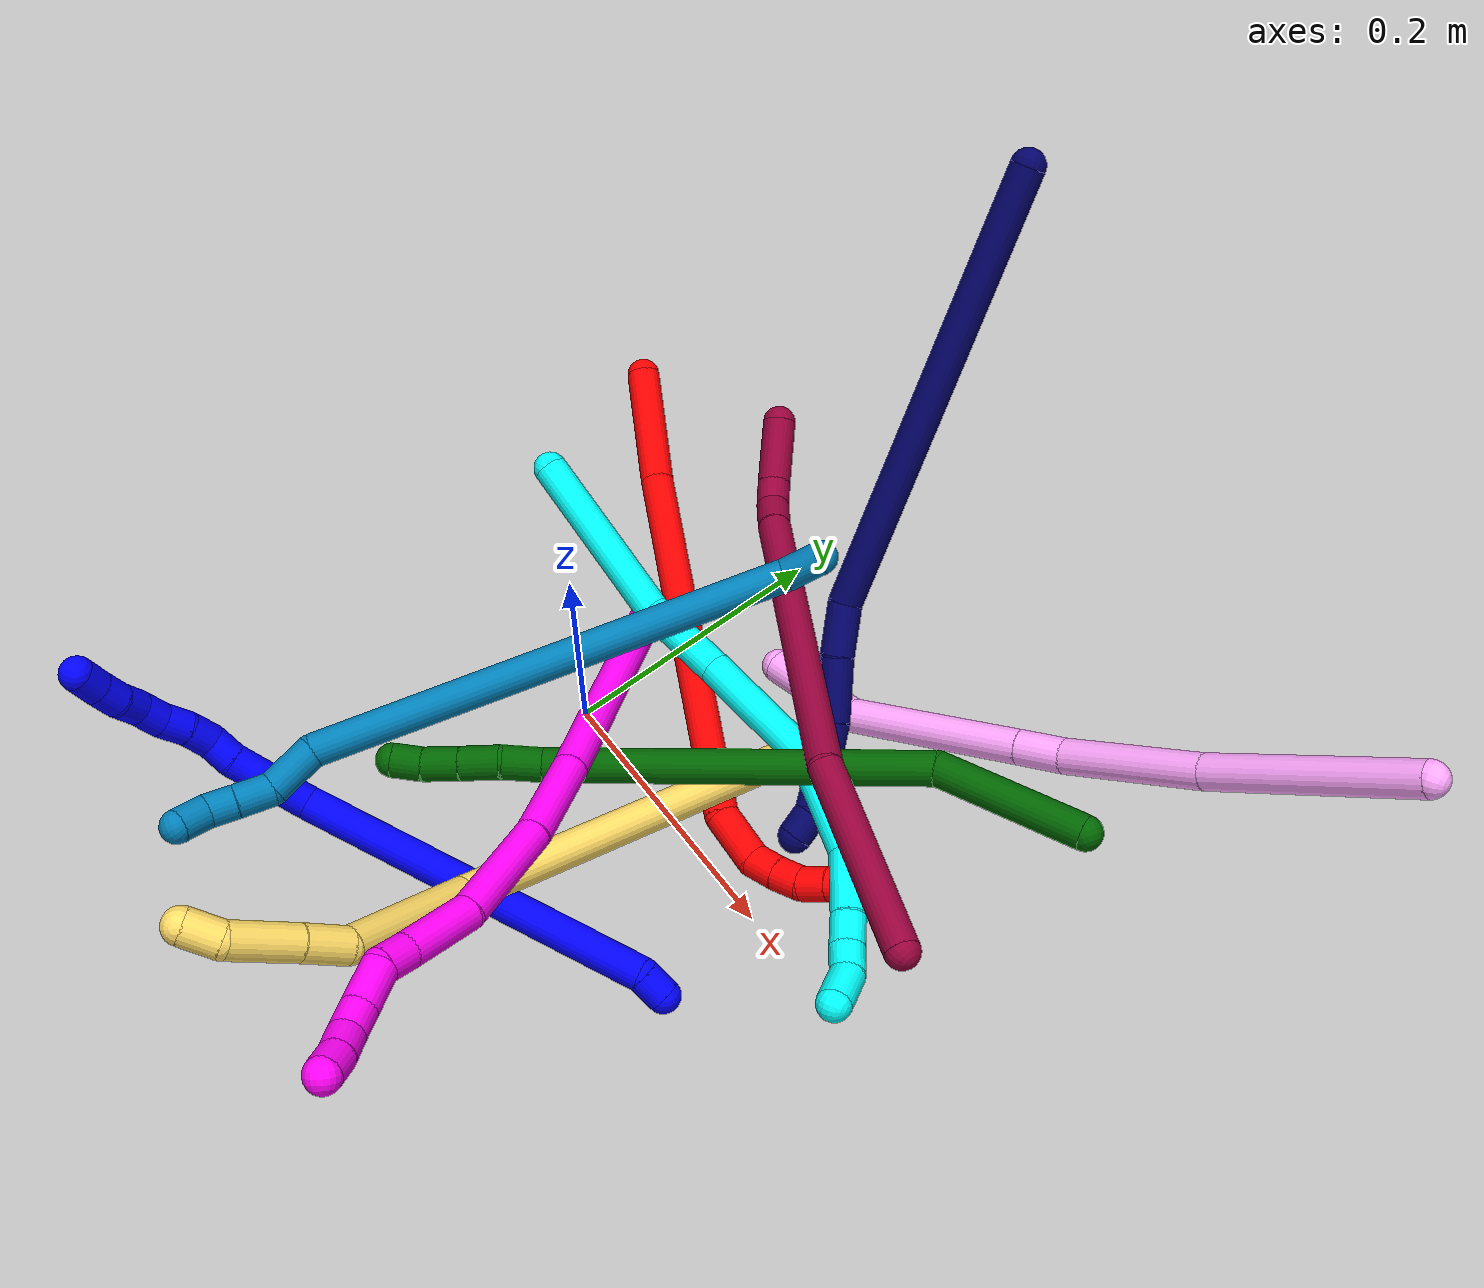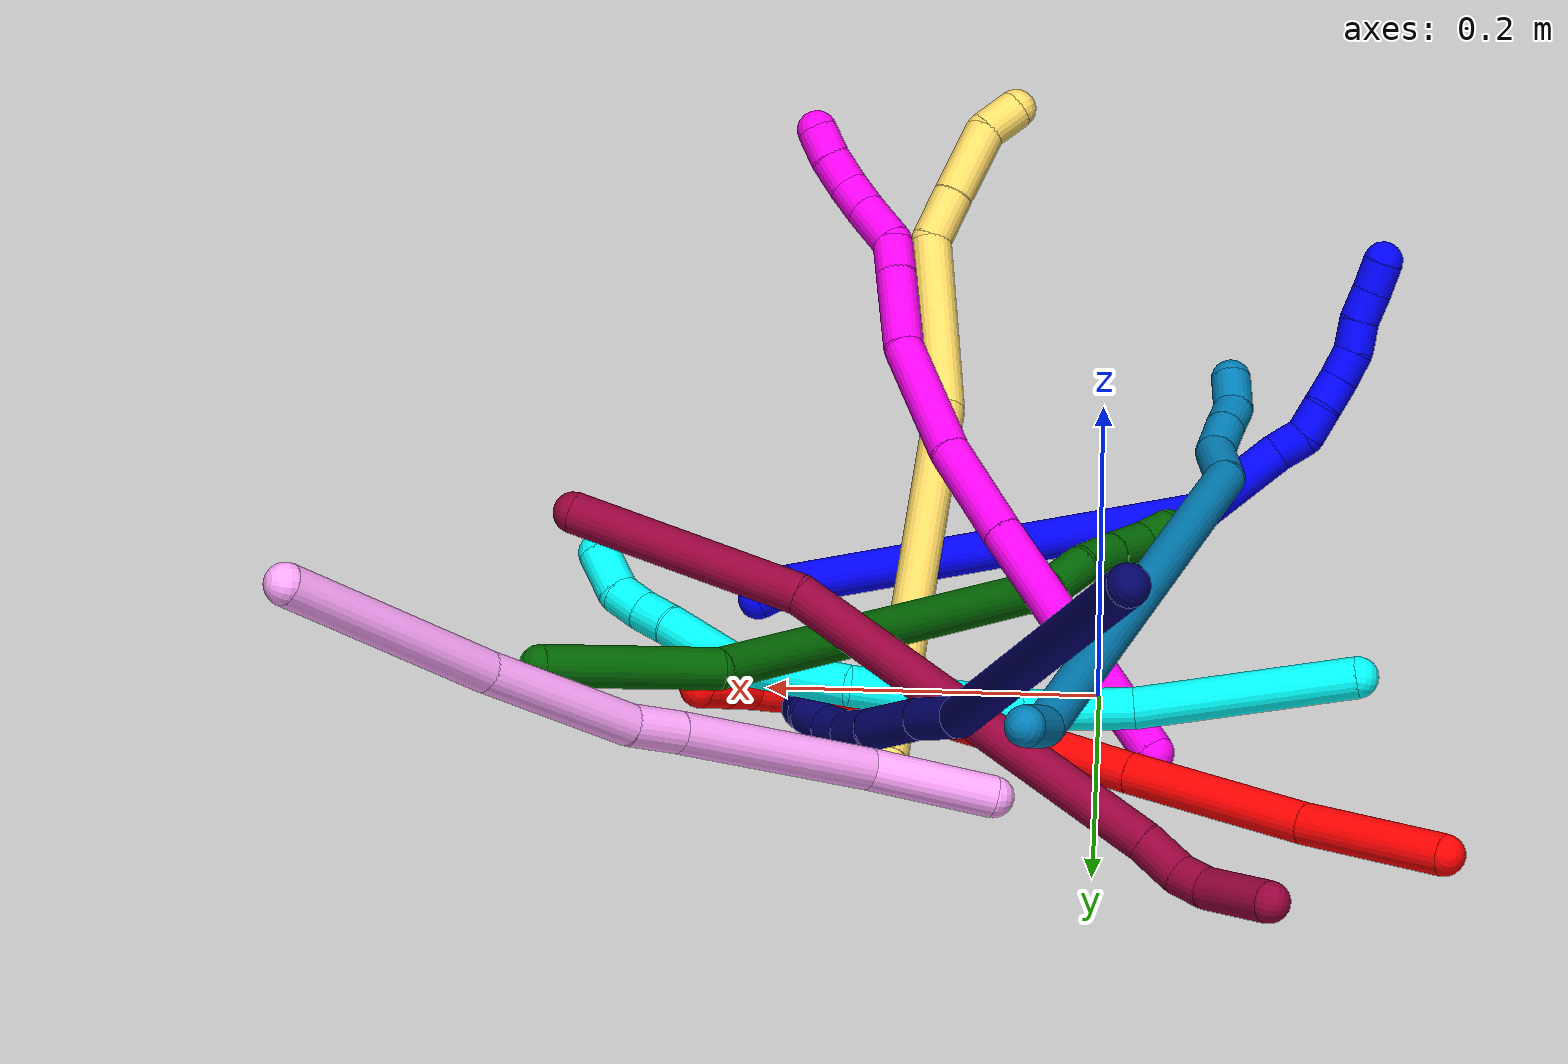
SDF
<sdf version="1.7">
 <world name="default">
  <plugin name="TubeGeneratorPlugin" filename="libtube_generator_plugin.so"/>
  <model name="photoneo_s_sensor">
   <static>1</static>
   <pose>0 0 2 1.57079 1.57079 3.14159</pose>
   <link name="link">
    <inertial><mass>0.1</mass></inertial>
    <sensor name="sensor" type="depth">
     <update_rate>30</update_rate>
     <camera>
      <horizontal_fov>1.22</horizontal_fov>
      <image><width>1920</width><height>1200</height><format>B8G8R8</format></image>
      <clip><near>0.1</near><far>2</far></clip>
      <depth_camera><output>points</output></depth_camera>
     </camera>
     <plugin name="camera_plugin" filename="libgazebo_ros_depth_camera.so">
      <baseline>0.2</baseline>
      <alwaysOn>1</alwaysOn>
      <updateRate>0.0</updateRate>
      <cameraName>camera_ir</cameraName>
      <imageTopicName>/camera/color/image_raw</imageTopicName>
      <cameraInfoTopicName>/camera/color/camera_info</cameraInfoTopicName>
      <depthImageTopicName>/camera/depth/image_raw</depthImageTopicName>
      <depthImageCameraInfoTopicName>/camera/depth/camera_info</depthImageCameraInfoTopicName>
      <pointCloudTopicName>/camera/depth/points</pointCloudTopicName>
      <frameName>fr_optical</frameName>
      <pointCloudCutoff>0.1</pointCloudCutoff>
      <pointCloudCutoffMax>2.0</pointCloudCutoffMax>
      <distortionK1>0</distortionK1>
      <distortionK2>0</distortionK2>
      <distortionK3>0</distortionK3>
      <distortionT1>0</distortionT1>
      <distortionT2>0</distortionT2>
      <CxPrime>0</CxPrime>
      <Cx>0</Cx>
      <Cy>0</Cy>
      <focalLength>0</focalLength>
      <hackBaseline>0</hackBaseline>
     </plugin>
    </sensor>
   </link>
  </model>
  <gravity>0 0 -9.8</gravity>
  <magnetic_field>6e-06 2.3e-05 -4.2e-05</magnetic_field>
  <atmosphere type="adiabatic"/>
  <physics name="default_physics" default="0" type="ode">
   <max_step_size>0.003</max_step_size>
   <real_time_factor>1</real_time_factor>
   <real_time_update_rate>1000</real_time_update_rate>
   <max_contacts>10000</max_contacts>
   <ode>
    <solver>
     <type>quick</type>
     <iters>100</iters>
     <sor>1.3</sor>
     <use_dynamic_moi_rescaling>0</use_dynamic_moi_rescaling>
    </solver>
    <constraints>
     <contact_max_correcting_vel>0</contact_max_correcting_vel>
     <contact_surface_layer>0.001</contact_surface_layer>
     <cfm>0</cfm>
     <erp>0.2</erp>
    </constraints>
   </ode>
  </physics>
  <scene><ambient>0.4 0.4 0.4 1</ambient><background>0.7 0.7 0.7 1</background><shadows>0</shadows></scene>
  <audio><device>default</device></audio>
  <spherical_coordinates>
   <surface_model>EARTH_WGS84</surface_model>
   <latitude_deg>0</latitude_deg>
   <longitude_deg>0</longitude_deg>
   <elevation>0</elevation>
   <heading_deg>0</heading_deg>
  </spherical_coordinates>
  <model name="bin">
   <static>1</static>
   <link name="bottom">
    <collision name="collision-bottom">
     <pose>0 0 -0.01 0 -0 0</pose>
     <geometry><box><size>0.8 0.6 0.02</size></box></geometry>
     <surface>
      <friction><ode><mu>100</mu><mu2>100</mu2></ode></friction>
      <contact><collide_bitmask>65535</collide_bitmask></contact>
     </surface>
    </collision>
   </link>
   <link name="west_wall">
    <collision name="collision-west_wall">
     <pose>-0.41 0 0.1 0 -0 0</pose>
     <geometry><box><size>0.02 0.6 0.2</size></box></geometry>
     <surface>
      <friction><ode><mu>100</mu><mu2>100</mu2></ode></friction>
      <contact><collide_bitmask>65535</collide_bitmask></contact>
     </surface>
    </collision>
   </link>
   <link name="east_wall">
    <collision name="collision-east_wall">
     <pose>0.41 0 0.1 0 -0 0</pose>
     <geometry><box><size>0.02 0.6 0.2</size></box></geometry>
     <surface>
      <friction><ode><mu>100</mu><mu2>100</mu2></ode></friction>
      <contact><collide_bitmask>65535</collide_bitmask></contact>
     </surface>
    </collision>
   </link>
   <link name="south_wall">
    <collision name="collision-south_wall">
     <pose>0 -0.31 0.1 0 -0 0</pose>
     <geometry><box><size>0.8 0.02 0.2</size></box></geometry>
     <surface>
      <friction><ode><mu>100</mu><mu2>100</mu2></ode></friction>
      <contact><collide_bitmask>65535</collide_bitmask></contact>
     </surface>
    </collision>
   </link>
   <link name="north_wall">
    <collision name="collision-north_wall">
     <pose>0 0.31 0.1 0 -0 0</pose>
     <geometry><box><size>0.8 0.02 0.2</size></box></geometry>
     <surface>
      <friction><ode><mu>100</mu><mu2>100</mu2></ode></friction>
      <contact><collide_bitmask>65535</collide_bitmask></contact>
     </surface>
    </collision>
   </link>
  </model>
  <model name="1">
   <static>0</static>
   <link name="1">
    <collision name="collision-cylinder-e_1_1_4">
     <pose>-0.008423 -0.00355 -0.004879 2.51263 -0.949167 -2.01272</pose>
     <geometry><cylinder><radius>0.0125</radius><length>0.020721</length></cylinder></geometry>
     <surface>
      <friction><ode><mu>1.16</mu><mu2>1.16</mu2><slip1>0</slip1><slip2>0</slip2></ode></friction>
      <contact><ode><kp>1e+06</kp><kd>1</kd><max_vel>0</max_vel><min_depth>0.001</min_depth></ode></contact>
     </surface>
    </collision>
    <visual name="visual-cylinder-e_1_1_4">
     <pose>-0.008423 -0.00355 -0.004879 2.51263 -0.949167 -2.01272</pose>
     <geometry><cylinder><radius>0.0125</radius><length>0.020721</length></cylinder></geometry>
     <material><ambient>0 0 1 1</ambient></material>
    </visual>
    <collision name="collision-cylinder-e_2_4_5">
     <pose>-0.146684 -0.052605 -0.011258 1.60374 -1.23353 -1.26479</pose>
     <geometry><cylinder><radius>0.0125</radius><length>0.275181</length></cylinder></geometry>
     <surface>
      <friction><ode><mu>1.16</mu><mu2>1.16</mu2><slip1>0</slip1><slip2>0</slip2></ode></friction>
      <contact><ode><kp>1e+06</kp><kd>1</kd><max_vel>0</max_vel><min_depth>0.001</min_depth></ode></contact>
     </surface>
    </collision>
    <visual name="visual-cylinder-e_2_4_5">
     <pose>-0.146684 -0.052605 -0.011258 1.60374 -1.23353 -1.26479</pose>
     <geometry><cylinder><radius>0.0125</radius><length>0.275181</length></cylinder></geometry>
     <material><ambient>0 0 1 1</ambient></material>
    </visual>
    <collision name="collision-cylinder-e_3_5_6">
     <pose>-0.304304 -0.10016 -0.026616 2.99471 -1.10373 -2.90372</pose>
     <geometry><cylinder><radius>0.0125</radius><length>0.062227</length></cylinder></geometry>
     <surface>
      <friction><ode><mu>1.16</mu><mu2>1.16</mu2><slip1>0</slip1><slip2>0</slip2></ode></friction>
      <contact><ode><kp>1e+06</kp><kd>1</kd><max_vel>0</max_vel><min_depth>0.001</min_depth></ode></contact>
     </surface>
    </collision>
    <visual name="visual-cylinder-e_3_5_6">
     <pose>-0.304304 -0.10016 -0.026616 2.99471 -1.10373 -2.90372</pose>
     <geometry><cylinder><radius>0.0125</radius><length>0.062227</length></cylinder></geometry>
     <material><ambient>0 0 1 1</ambient></material>
    </visual>
    <collision name="collision-cylinder-e_4_6_7">
     <pose>-0.340377 -0.104793 -0.045662 2.67966 -0.96079 -2.29378</pose>
     <geometry><cylinder><radius>0.0125</radius><length>0.020231</length></cylinder></geometry>
     <surface>
      <friction><ode><mu>1.16</mu><mu2>1.16</mu2><slip1>0</slip1><slip2>0</slip2></ode></friction>
      <contact><ode><kp>1e+06</kp><kd>1</kd><max_vel>0</max_vel><min_depth>0.001</min_depth></ode></contact>
     </surface>
    </collision>
    <visual name="visual-cylinder-e_4_6_7">
     <pose>-0.340377 -0.104793 -0.045662 2.67966 -0.96079 -2.29378</pose>
     <geometry><cylinder><radius>0.0125</radius><length>0.020231</length></cylinder></geometry>
     <material><ambient>0 0 1 1</ambient></material>
    </visual>
    <collision name="collision-cylinder-e_5_7_8">
     <pose>-0.35622 -0.105274 -0.058106 -2.8596 -0.785236 2.48119</pose>
     <geometry><cylinder><radius>0.0125</radius><length>0.021365</length></cylinder></geometry>
     <surface>
      <friction><ode><mu>1.16</mu><mu2>1.16</mu2><slip1>0</slip1><slip2>0</slip2></ode></friction>
      <contact><ode><kp>1e+06</kp><kd>1</kd><max_vel>0</max_vel><min_depth>0.001</min_depth></ode></contact>
     </surface>
    </collision>
    <visual name="visual-cylinder-e_5_7_8">
     <pose>-0.35622 -0.105274 -0.058106 -2.8596 -0.785236 2.48119</pose>
     <geometry><cylinder><radius>0.0125</radius><length>0.021365</length></cylinder></geometry>
     <material><ambient>0 0 1 1</ambient></material>
    </visual>
    <collision name="collision-cylinder-e_6_8_9">
     <pose>-0.371842 -0.100452 -0.070789 -2.67704 -0.925858 2.25642</pose>
     <geometry><cylinder><radius>0.0125</radius><length>0.020195</length></cylinder></geometry>
     <surface>
      <friction><ode><mu>1.16</mu><mu2>1.16</mu2><slip1>0</slip1><slip2>0</slip2></ode></friction>
      <contact><ode><kp>1e+06</kp><kd>1</kd><max_vel>0</max_vel><min_depth>0.001</min_depth></ode></contact>
     </surface>
    </collision>
    <visual name="visual-cylinder-e_6_8_9">
     <pose>-0.371842 -0.100452 -0.070789 -2.67704 -0.925858 2.25642</pose>
     <geometry><cylinder><radius>0.0125</radius><length>0.020195</length></cylinder></geometry>
     <material><ambient>0 0 1 1</ambient></material>
    </visual>
    <collision name="collision-cylinder-e_7_9_10">
     <pose>-0.386521 -0.095423 -0.083394 -2.83039 -0.719735 2.35156</pose>
     <geometry><cylinder><radius>0.0125</radius><length>0.020054</length></cylinder></geometry>
     <surface>
      <friction><ode><mu>1.16</mu><mu2>1.16</mu2><slip1>0</slip1><slip2>0</slip2></ode></friction>
      <contact><ode><kp>1e+06</kp><kd>1</kd><max_vel>0</max_vel><min_depth>0.001</min_depth></ode></contact>
     </surface>
    </collision>
    <visual name="visual-cylinder-e_7_9_10">
     <pose>-0.386521 -0.095423 -0.083394 -2.83039 -0.719735 2.35156</pose>
     <geometry><cylinder><radius>0.0125</radius><length>0.020054</length></cylinder></geometry>
     <material><ambient>0 0 1 1</ambient></material>
    </visual>
    <collision name="collision-cylinder-e_8_10_11">
     <pose>-0.397847 -0.088626 -0.098177 -2.60836 -0.490594 1.48382</pose>
     <geometry><cylinder><radius>0.0125</radius><length>0.020022</length></cylinder></geometry>
     <surface>
      <friction><ode><mu>1.16</mu><mu2>1.16</mu2><slip1>0</slip1><slip2>0</slip2></ode></friction>
      <contact><ode><kp>1e+06</kp><kd>1</kd><max_vel>0</max_vel><min_depth>0.001</min_depth></ode></contact>
     </surface>
    </collision>
    <visual name="visual-cylinder-e_8_10_11">
     <pose>-0.397847 -0.088626 -0.098177 -2.60836 -0.490594 1.48382</pose>
     <geometry><cylinder><radius>0.0125</radius><length>0.020022</length></cylinder></geometry>
     <material><ambient>0 0 1 1</ambient></material>
    </visual>
    <collision name="collision-cylinder-e_9_11_12">
     <pose>-0.40827 -0.081605 -0.113594 -2.82816 -0.607254 2.20739</pose>
     <geometry><cylinder><radius>0.0125</radius><length>0.020001</length></cylinder></geometry>
     <surface>
      <friction><ode><mu>1.16</mu><mu2>1.16</mu2><slip1>0</slip1><slip2>0</slip2></ode></friction>
      <contact><ode><kp>1e+06</kp><kd>1</kd><max_vel>0</max_vel><min_depth>0.001</min_depth></ode></contact>
     </surface>
    </collision>
    <visual name="visual-cylinder-e_9_11_12">
     <pose>-0.40827 -0.081605 -0.113594 -2.82816 -0.607254 2.20739</pose>
     <geometry><cylinder><radius>0.0125</radius><length>0.020001</length></cylinder></geometry>
     <material><ambient>0 0 1 1</ambient></material>
    </visual>
    <collision name="collision-cylinder-e_10_12_2">
     <pose>-0.418989 -0.076476 -0.129661 -2.83677 -0.524984 2.10295</pose>
     <geometry><cylinder><radius>0.0125</radius><length>0.020002</length></cylinder></geometry>
     <surface>
      <friction><ode><mu>1.16</mu><mu2>1.16</mu2><slip1>0</slip1><slip2>0</slip2></ode></friction>
      <contact><ode><kp>1e+06</kp><kd>1</kd><max_vel>0</max_vel><min_depth>0.001</min_depth></ode></contact>
     </surface>
    </collision>
    <visual name="visual-cylinder-e_10_12_2">
     <pose>-0.418989 -0.076476 -0.129661 -2.83677 -0.524984 2.10295</pose>
     <geometry><cylinder><radius>0.0125</radius><length>0.020002</length></cylinder></geometry>
     <material><ambient>0 0 1 1</ambient></material>
    </visual>
    <collision name="collision-sphere-2">
     <pose>-0.424002 -0.073878 -0.137917 0 -0 0</pose>
     <geometry><sphere><radius>0.0125</radius></sphere></geometry>
     <surface>
      <friction><ode><mu>1.16</mu><mu2>1.16</mu2><slip1>0</slip1><slip2>0</slip2></ode></friction>
      <contact><ode><kp>1e+06</kp><kd>1</kd><max_vel>0</max_vel><min_depth>0.001</min_depth></ode></contact>
     </surface>
    </collision>
    <visual name="visual-sphere-2">
     <pose>-0.424002 -0.073878 -0.137917 0 -0 0</pose>
     <geometry><sphere><radius>0.0125</radius></sphere></geometry>
     <material><ambient>0 0 1 1</ambient></material>
    </visual>
    <collision name="collision-sphere-12">
     <pose>-0.413977 -0.079073 -0.121406 0 -0 0</pose>
     <geometry><sphere><radius>0.0125</radius></sphere></geometry>
     <surface>
      <friction><ode><mu>1.16</mu><mu2>1.16</mu2><slip1>0</slip1><slip2>0</slip2></ode></friction>
      <contact><ode><kp>1e+06</kp><kd>1</kd><max_vel>0</max_vel><min_depth>0.001</min_depth></ode></contact>
     </surface>
    </collision>
    <visual name="visual-sphere-12">
     <pose>-0.413977 -0.079073 -0.121406 0 -0 0</pose>
     <geometry><sphere><radius>0.0125</radius></sphere></geometry>
     <material><ambient>0 0 1 1</ambient></material>
    </visual>
    <collision name="collision-sphere-11">
     <pose>-0.402564 -0.084137 -0.105781 0 -0 0</pose>
     <geometry><sphere><radius>0.0125</radius></sphere></geometry>
     <surface>
      <friction><ode><mu>1.16</mu><mu2>1.16</mu2><slip1>0</slip1><slip2>0</slip2></ode></friction>
      <contact><ode><kp>1e+06</kp><kd>1</kd><max_vel>0</max_vel><min_depth>0.001</min_depth></ode></contact>
     </surface>
    </collision>
    <visual name="visual-sphere-11">
     <pose>-0.402564 -0.084137 -0.105781 0 -0 0</pose>
     <geometry><sphere><radius>0.0125</radius></sphere></geometry>
     <material><ambient>0 0 1 1</ambient></material>
    </visual>
    <collision name="collision-sphere-10">
     <pose>-0.393131 -0.093114 -0.090572 0 -0 0</pose>
     <geometry><sphere><radius>0.0125</radius></sphere></geometry>
     <surface>
      <friction><ode><mu>1.16</mu><mu2>1.16</mu2><slip1>0</slip1><slip2>0</slip2></ode></friction>
      <contact><ode><kp>1e+06</kp><kd>1</kd><max_vel>0</max_vel><min_depth>0.001</min_depth></ode></contact>
     </surface>
    </collision>
    <visual name="visual-sphere-10">
     <pose>-0.393131 -0.093114 -0.090572 0 -0 0</pose>
     <geometry><sphere><radius>0.0125</radius></sphere></geometry>
     <material><ambient>0 0 1 1</ambient></material>
    </visual>
    <collision name="collision-sphere-9">
     <pose>-0.379911 -0.097732 -0.076216 0 -0 0</pose>
     <geometry><sphere><radius>0.0125</radius></sphere></geometry>
     <surface>
      <friction><ode><mu>1.16</mu><mu2>1.16</mu2><slip1>0</slip1><slip2>0</slip2></ode></friction>
      <contact><ode><kp>1e+06</kp><kd>1</kd><max_vel>0</max_vel><min_depth>0.001</min_depth></ode></contact>
     </surface>
    </collision>
    <visual name="visual-sphere-9">
     <pose>-0.379911 -0.097732 -0.076216 0 -0 0</pose>
     <geometry><sphere><radius>0.0125</radius></sphere></geometry>
     <material><ambient>0 0 1 1</ambient></material>
    </visual>
    <collision name="collision-sphere-4">
     <pose>-0.016845 -0.007099 -0.009758 0 -0 0</pose>
     <geometry><sphere><radius>0.0125</radius></sphere></geometry>
     <surface>
      <friction><ode><mu>1.16</mu><mu2>1.16</mu2><slip1>0</slip1><slip2>0</slip2></ode></friction>
      <contact><ode><kp>1e+06</kp><kd>1</kd><max_vel>0</max_vel><min_depth>0.001</min_depth></ode></contact>
     </surface>
    </collision>
    <visual name="visual-sphere-4">
     <pose>-0.016845 -0.007099 -0.009758 0 -0 0</pose>
     <geometry><sphere><radius>0.0125</radius></sphere></geometry>
     <material><ambient>0 0 1 1</ambient></material>
    </visual>
    <collision name="collision-sphere-1">
     <geometry><sphere><radius>0.0125</radius></sphere></geometry>
     <surface>
      <friction><ode><mu>1.16</mu><mu2>1.16</mu2><slip1>0</slip1><slip2>0</slip2></ode></friction>
      <contact><ode><kp>1e+06</kp><kd>1</kd><max_vel>0</max_vel><min_depth>0.001</min_depth></ode></contact>
     </surface>
    </collision>
    <visual name="visual-sphere-1">
     <geometry><sphere><radius>0.0125</radius></sphere></geometry>
     <material><ambient>0 0 1 1</ambient></material>
    </visual>
    <collision name="collision-sphere-8">
     <pose>-0.363772 -0.103171 -0.065363 0 -0 0</pose>
     <geometry><sphere><radius>0.0125</radius></sphere></geometry>
     <surface>
      <friction><ode><mu>1.16</mu><mu2>1.16</mu2><slip1>0</slip1><slip2>0</slip2></ode></friction>
      <contact><ode><kp>1e+06</kp><kd>1</kd><max_vel>0</max_vel><min_depth>0.001</min_depth></ode></contact>
     </surface>
    </collision>
    <visual name="visual-sphere-8">
     <pose>-0.363772 -0.103171 -0.065363 0 -0 0</pose>
     <geometry><sphere><radius>0.0125</radius></sphere></geometry>
     <material><ambient>0 0 1 1</ambient></material>
    </visual>
    <collision name="collision-sphere-5">
     <pose>-0.276523 -0.09811 -0.012758 0 -0 0</pose>
     <geometry><sphere><radius>0.0125</radius></sphere></geometry>
     <surface>
      <friction><ode><mu>1.16</mu><mu2>1.16</mu2><slip1>0</slip1><slip2>0</slip2></ode></friction>
      <contact><ode><kp>1e+06</kp><kd>1</kd><max_vel>0</max_vel><min_depth>0.001</min_depth></ode></contact>
     </surface>
    </collision>
    <visual name="visual-sphere-5">
     <pose>-0.276523 -0.09811 -0.012758 0 -0 0</pose>
     <geometry><sphere><radius>0.0125</radius></sphere></geometry>
     <material><ambient>0 0 1 1</ambient></material>
    </visual>
    <collision name="collision-sphere-6">
     <pose>-0.332086 -0.102211 -0.040475 0 -0 0</pose>
     <geometry><sphere><radius>0.0125</radius></sphere></geometry>
     <surface>
      <friction><ode><mu>1.16</mu><mu2>1.16</mu2><slip1>0</slip1><slip2>0</slip2></ode></friction>
      <contact><ode><kp>1e+06</kp><kd>1</kd><max_vel>0</max_vel><min_depth>0.001</min_depth></ode></contact>
     </surface>
    </collision>
    <visual name="visual-sphere-6">
     <pose>-0.332086 -0.102211 -0.040475 0 -0 0</pose>
     <geometry><sphere><radius>0.0125</radius></sphere></geometry>
     <material><ambient>0 0 1 1</ambient></material>
    </visual>
    <collision name="collision-sphere-7">
     <pose>-0.348667 -0.107376 -0.05085 0 -0 0</pose>
     <geometry><sphere><radius>0.0125</radius></sphere></geometry>
     <surface>
      <friction><ode><mu>1.16</mu><mu2>1.16</mu2><slip1>0</slip1><slip2>0</slip2></ode></friction>
      <contact><ode><kp>1e+06</kp><kd>1</kd><max_vel>0</max_vel><min_depth>0.001</min_depth></ode></contact>
     </surface>
    </collision>
    <visual name="visual-sphere-7">
     <pose>-0.348667 -0.107376 -0.05085 0 -0 0</pose>
     <geometry><sphere><radius>0.0125</radius></sphere></geometry>
     <material><ambient>0 0 1 1</ambient></material>
    </visual>
    <inertial>
     <pose>-0.22749 -0.06806 -0.033907 0 -0 0</pose>
     <mass>0.5</mass>
     <inertia>
      <ixx>-0.000423</ixx>
      <ixy>0</ixy>
      <ixz>0</ixz>
      <iyy>0.001029</iyy>
      <iyz>0</iyz>
      <izz>0.002244</izz>
     </inertia>
    </inertial>
   </link>
   <pose>0.210829 -0.084868 0.011496 2.84462 0.05961 0.751478</pose>
  </model>
  <model name="2">
   <static>0</static>
   <link name="2">
    <collision name="collision-cylinder-e_1_1_4">
     <pose>0.030949 -0.01481 -0.031613 2.70348 0.72533 2.08041</pose>
     <geometry><cylinder><radius>0.0125</radius><length>0.093306</length></cylinder></geometry>
     <surface>
      <friction><ode><mu>1.16</mu><mu2>1.16</mu2><slip1>0</slip1><slip2>0</slip2></ode></friction>
      <contact><ode><kp>1e+06</kp><kd>1</kd><max_vel>0</max_vel><min_depth>0.001</min_depth></ode></contact>
     </surface>
    </collision>
    <visual name="visual-cylinder-e_1_1_4">
     <pose>0.030949 -0.01481 -0.031613 2.70348 0.72533 2.08041</pose>
     <geometry><cylinder><radius>0.0125</radius><length>0.093306</length></cylinder></geometry>
     <material><ambient>1 0 0 1</ambient></material>
    </visual>
    <collision name="collision-cylinder-e_2_4_5">
     <pose>0.102061 -0.051622 -0.097663 2.57306 0.776726 1.90131</pose>
     <geometry><cylinder><radius>0.0125</radius><length>0.114597</length></cylinder></geometry>
     <surface>
      <friction><ode><mu>1.16</mu><mu2>1.16</mu2><slip1>0</slip1><slip2>0</slip2></ode></friction>
      <contact><ode><kp>1e+06</kp><kd>1</kd><max_vel>0</max_vel><min_depth>0.001</min_depth></ode></contact>
     </surface>
    </collision>
    <visual name="visual-cylinder-e_2_4_5">
     <pose>0.102061 -0.051622 -0.097663 2.57306 0.776726 1.90131</pose>
     <geometry><cylinder><radius>0.0125</radius><length>0.114597</length></cylinder></geometry>
     <material><ambient>1 0 0 1</ambient></material>
    </visual>
    <collision name="collision-cylinder-e_3_5_6">
     <pose>0.201324 -0.107155 -0.181868 2.5487 0.77775 1.86041</pose>
     <geometry><cylinder><radius>0.0125</radius><length>0.168451</length></cylinder></geometry>
     <surface>
      <friction><ode><mu>1.16</mu><mu2>1.16</mu2><slip1>0</slip1><slip2>0</slip2></ode></friction>
      <contact><ode><kp>1e+06</kp><kd>1</kd><max_vel>0</max_vel><min_depth>0.001</min_depth></ode></contact>
     </surface>
    </collision>
    <visual name="visual-cylinder-e_3_5_6">
     <pose>0.201324 -0.107155 -0.181868 2.5487 0.77775 1.86041</pose>
     <geometry><cylinder><radius>0.0125</radius><length>0.168451</length></cylinder></geometry>
     <material><ambient>1 0 0 1</ambient></material>
    </visual>
    <collision name="collision-cylinder-e_4_6_7">
     <pose>0.279253 -0.144492 -0.238006 2.60297 1.19545 2.37124</pose>
     <geometry><cylinder><radius>0.0125</radius><length>0.040479</length></cylinder></geometry>
     <surface>
      <friction><ode><mu>1.16</mu><mu2>1.16</mu2><slip1>0</slip1><slip2>0</slip2></ode></friction>
      <contact><ode><kp>1e+06</kp><kd>1</kd><max_vel>0</max_vel><min_depth>0.001</min_depth></ode></contact>
     </surface>
    </collision>
    <visual name="visual-cylinder-e_4_6_7">
     <pose>0.279253 -0.144492 -0.238006 2.60297 1.19545 2.37124</pose>
     <geometry><cylinder><radius>0.0125</radius><length>0.040479</length></cylinder></geometry>
     <material><ambient>1 0 0 1</ambient></material>
    </visual>
    <collision name="collision-cylinder-e_5_7_8">
     <pose>0.308418 -0.150698 -0.243122 1.08958 1.31458 0.874889</pose>
     <geometry><cylinder><radius>0.0125</radius><length>0.021366</length></cylinder></geometry>
     <surface>
      <friction><ode><mu>1.16</mu><mu2>1.16</mu2><slip1>0</slip1><slip2>0</slip2></ode></friction>
      <contact><ode><kp>1e+06</kp><kd>1</kd><max_vel>0</max_vel><min_depth>0.001</min_depth></ode></contact>
     </surface>
    </collision>
    <visual name="visual-cylinder-e_5_7_8">
     <pose>0.308418 -0.150698 -0.243122 1.08958 1.31458 0.874889</pose>
     <geometry><cylinder><radius>0.0125</radius><length>0.021366</length></cylinder></geometry>
     <material><ambient>1 0 0 1</ambient></material>
    </visual>
    <collision name="collision-cylinder-e_6_8_9">
     <pose>0.328295 -0.155304 -0.239694 0.792434 1.2569 0.590291</pose>
     <geometry><cylinder><radius>0.0125</radius><length>0.020066</length></cylinder></geometry>
     <surface>
      <friction><ode><mu>1.16</mu><mu2>1.16</mu2><slip1>0</slip1><slip2>0</slip2></ode></friction>
      <contact><ode><kp>1e+06</kp><kd>1</kd><max_vel>0</max_vel><min_depth>0.001</min_depth></ode></contact>
     </surface>
    </collision>
    <visual name="visual-cylinder-e_6_8_9">
     <pose>0.328295 -0.155304 -0.239694 0.792434 1.2569 0.590291</pose>
     <geometry><cylinder><radius>0.0125</radius><length>0.020066</length></cylinder></geometry>
     <material><ambient>1 0 0 1</ambient></material>
    </visual>
    <collision name="collision-cylinder-e_7_9_10">
     <pose>0.34649 -0.158863 -0.231939 0.237995 0.984887 0.128122</pose>
     <geometry><cylinder><radius>0.0125</radius><length>0.020768</length></cylinder></geometry>
     <surface>
      <friction><ode><mu>1.16</mu><mu2>1.16</mu2><slip1>0</slip1><slip2>0</slip2></ode></friction>
      <contact><ode><kp>1e+06</kp><kd>1</kd><max_vel>0</max_vel><min_depth>0.001</min_depth></ode></contact>
     </surface>
    </collision>
    <visual name="visual-cylinder-e_7_9_10">
     <pose>0.34649 -0.158863 -0.231939 0.237995 0.984887 0.128122</pose>
     <geometry><cylinder><radius>0.0125</radius><length>0.020768</length></cylinder></geometry>
     <material><ambient>1 0 0 1</ambient></material>
    </visual>
    <collision name="collision-cylinder-e_8_10_2">
     <pose>0.364251 -0.161528 -0.221338 0.255519 1.053 0.149052</pose>
     <geometry><cylinder><radius>0.0125</radius><length>0.020967</length></cylinder></geometry>
     <surface>
      <friction><ode><mu>1.16</mu><mu2>1.16</mu2><slip1>0</slip1><slip2>0</slip2></ode></friction>
      <contact><ode><kp>1e+06</kp><kd>1</kd><max_vel>0</max_vel><min_depth>0.001</min_depth></ode></contact>
     </surface>
    </collision>
    <visual name="visual-cylinder-e_8_10_2">
     <pose>0.364251 -0.161528 -0.221338 0.255519 1.053 0.149052</pose>
     <geometry><cylinder><radius>0.0125</radius><length>0.020967</length></cylinder></geometry>
     <material><ambient>1 0 0 1</ambient></material>
    </visual>
    <collision name="collision-sphere-2">
     <pose>0.37336 -0.16284 -0.216318 0 -0 0</pose>
     <geometry><sphere><radius>0.0125</radius></sphere></geometry>
     <surface>
      <friction><ode><mu>1.16</mu><mu2>1.16</mu2><slip1>0</slip1><slip2>0</slip2></ode></friction>
      <contact><ode><kp>1e+06</kp><kd>1</kd><max_vel>0</max_vel><min_depth>0.001</min_depth></ode></contact>
     </surface>
    </collision>
    <visual name="visual-sphere-2">
     <pose>0.37336 -0.16284 -0.216318 0 -0 0</pose>
     <geometry><sphere><radius>0.0125</radius></sphere></geometry>
     <material><ambient>1 0 0 1</ambient></material>
    </visual>
    <collision name="collision-sphere-10">
     <pose>0.355141 -0.160217 -0.226359 0 -0 0</pose>
     <geometry><sphere><radius>0.0125</radius></sphere></geometry>
     <surface>
      <friction><ode><mu>1.16</mu><mu2>1.16</mu2><slip1>0</slip1><slip2>0</slip2></ode></friction>
      <contact><ode><kp>1e+06</kp><kd>1</kd><max_vel>0</max_vel><min_depth>0.001</min_depth></ode></contact>
     </surface>
    </collision>
    <visual name="visual-sphere-10">
     <pose>0.355141 -0.160217 -0.226359 0 -0 0</pose>
     <geometry><sphere><radius>0.0125</radius></sphere></geometry>
     <material><ambient>1 0 0 1</ambient></material>
    </visual>
    <collision name="collision-sphere-9">
     <pose>0.337838 -0.15751 -0.237519 0 -0 0</pose>
     <geometry><sphere><radius>0.0125</radius></sphere></geometry>
     <surface>
      <friction><ode><mu>1.16</mu><mu2>1.16</mu2><slip1>0</slip1><slip2>0</slip2></ode></friction>
      <contact><ode><kp>1e+06</kp><kd>1</kd><max_vel>0</max_vel><min_depth>0.001</min_depth></ode></contact>
     </surface>
    </collision>
    <visual name="visual-sphere-9">
     <pose>0.337838 -0.15751 -0.237519 0 -0 0</pose>
     <geometry><sphere><radius>0.0125</radius></sphere></geometry>
     <material><ambient>1 0 0 1</ambient></material>
    </visual>
    <collision name="collision-sphere-4">
     <pose>0.061898 -0.029619 -0.063225 0 -0 0</pose>
     <geometry><sphere><radius>0.0125</radius></sphere></geometry>
     <surface>
      <friction><ode><mu>1.16</mu><mu2>1.16</mu2><slip1>0</slip1><slip2>0</slip2></ode></friction>
      <contact><ode><kp>1e+06</kp><kd>1</kd><max_vel>0</max_vel><min_depth>0.001</min_depth></ode></contact>
     </surface>
    </collision>
    <visual name="visual-sphere-4">
     <pose>0.061898 -0.029619 -0.063225 0 -0 0</pose>
     <geometry><sphere><radius>0.0125</radius></sphere></geometry>
     <material><ambient>1 0 0 1</ambient></material>
    </visual>
    <collision name="collision-sphere-1">
     <geometry><sphere><radius>0.0125</radius></sphere></geometry>
     <surface>
      <friction><ode><mu>1.16</mu><mu2>1.16</mu2><slip1>0</slip1><slip2>0</slip2></ode></friction>
      <contact><ode><kp>1e+06</kp><kd>1</kd><max_vel>0</max_vel><min_depth>0.001</min_depth></ode></contact>
     </surface>
    </collision>
    <visual name="visual-sphere-1">
     <geometry><sphere><radius>0.0125</radius></sphere></geometry>
     <material><ambient>1 0 0 1</ambient></material>
    </visual>
    <collision name="collision-sphere-8">
     <pose>0.318752 -0.153098 -0.241869 0 -0 0</pose>
     <geometry><sphere><radius>0.0125</radius></sphere></geometry>
     <surface>
      <friction><ode><mu>1.16</mu><mu2>1.16</mu2><slip1>0</slip1><slip2>0</slip2></ode></friction>
      <contact><ode><kp>1e+06</kp><kd>1</kd><max_vel>0</max_vel><min_depth>0.001</min_depth></ode></contact>
     </surface>
    </collision>
    <visual name="visual-sphere-8">
     <pose>0.318752 -0.153098 -0.241869 0 -0 0</pose>
     <geometry><sphere><radius>0.0125</radius></sphere></geometry>
     <material><ambient>1 0 0 1</ambient></material>
    </visual>
    <collision name="collision-sphere-5">
     <pose>0.142225 -0.073624 -0.1321 0 -0 0</pose>
     <geometry><sphere><radius>0.0125</radius></sphere></geometry>
     <surface>
      <friction><ode><mu>1.16</mu><mu2>1.16</mu2><slip1>0</slip1><slip2>0</slip2></ode></friction>
      <contact><ode><kp>1e+06</kp><kd>1</kd><max_vel>0</max_vel><min_depth>0.001</min_depth></ode></contact>
     </surface>
    </collision>
    <visual name="visual-sphere-5">
     <pose>0.142225 -0.073624 -0.1321 0 -0 0</pose>
     <geometry><sphere><radius>0.0125</radius></sphere></geometry>
     <material><ambient>1 0 0 1</ambient></material>
    </visual>
    <collision name="collision-sphere-6">
     <pose>0.260423 -0.140686 -0.231637 0 -0 0</pose>
     <geometry><sphere><radius>0.0125</radius></sphere></geometry>
     <surface>
      <friction><ode><mu>1.16</mu><mu2>1.16</mu2><slip1>0</slip1><slip2>0</slip2></ode></friction>
      <contact><ode><kp>1e+06</kp><kd>1</kd><max_vel>0</max_vel><min_depth>0.001</min_depth></ode></contact>
     </surface>
    </collision>
    <visual name="visual-sphere-6">
     <pose>0.260423 -0.140686 -0.231637 0 -0 0</pose>
     <geometry><sphere><radius>0.0125</radius></sphere></geometry>
     <material><ambient>1 0 0 1</ambient></material>
    </visual>
    <collision name="collision-sphere-7">
     <pose>0.298084 -0.148298 -0.244375 0 -0 0</pose>
     <geometry><sphere><radius>0.0125</radius></sphere></geometry>
     <surface>
      <friction><ode><mu>1.16</mu><mu2>1.16</mu2><slip1>0</slip1><slip2>0</slip2></ode></friction>
      <contact><ode><kp>1e+06</kp><kd>1</kd><max_vel>0</max_vel><min_depth>0.001</min_depth></ode></contact>
     </surface>
    </collision>
    <visual name="visual-sphere-7">
     <pose>0.298084 -0.148298 -0.244375 0 -0 0</pose>
     <geometry><sphere><radius>0.0125</radius></sphere></geometry>
     <material><ambient>1 0 0 1</ambient></material>
    </visual>
    <inertial>
     <pose>0.175622 -0.088438 -0.147747 0 -0 0</pose>
     <mass>0.5</mass>
     <inertia>
      <ixx>0.000304</ixx>
      <ixy>0</ixy>
      <ixz>0</ixz>
      <iyy>0.000792</iyy>
      <iyz>0</iyz>
      <izz>-0.000216</izz>
     </inertia>
    </inertial>
   </link>
   <pose>-0.203118 0.202607 0.023181 -0.99024 0.00556 0.319963</pose>
  </model>
  <model name="3">
   <static>0</static>
   <link name="3">
    <collision name="collision-cylinder-e_1_1_4">
     <pose>0.037939 0.007708 0.054569 -0.140324 0.602907 -0.043696</pose>
     <geometry><cylinder><radius>0.0125</radius><length>0.133814</length></cylinder></geometry>
     <surface>
      <friction><ode><mu>1.16</mu><mu2>1.16</mu2><slip1>0</slip1><slip2>0</slip2></ode></friction>
      <contact><ode><kp>1e+06</kp><kd>1</kd><max_vel>0</max_vel><min_depth>0.001</min_depth></ode></contact>
     </surface>
    </collision>
    <visual name="visual-cylinder-e_1_1_4">
     <pose>0.037939 0.007708 0.054569 -0.140324 0.602907 -0.043696</pose>
     <geometry><cylinder><radius>0.0125</radius><length>0.133814</length></cylinder></geometry>
     <material><ambient>0.003922 1 0.996078 1</ambient></material>
    </visual>
    <collision name="collision-cylinder-e_2_4_5">
     <pose>0.087547 0.017981 0.140359 -0.081979 0.356571 -0.014781</pose>
     <geometry><cylinder><radius>0.0125</radius><length>0.066859</length></cylinder></geometry>
     <surface>
      <friction><ode><mu>1.16</mu><mu2>1.16</mu2><slip1>0</slip1><slip2>0</slip2></ode></friction>
      <contact><ode><kp>1e+06</kp><kd>1</kd><max_vel>0</max_vel><min_depth>0.001</min_depth></ode></contact>
     </surface>
    </collision>
    <visual name="visual-cylinder-e_2_4_5">
     <pose>0.087547 0.017981 0.140359 -0.081979 0.356571 -0.014781</pose>
     <geometry><cylinder><radius>0.0125</radius><length>0.066859</length></cylinder></geometry>
     <material><ambient>0.003922 1 0.996078 1</ambient></material>
    </visual>
    <collision name="collision-cylinder-e_3_5_6">
     <pose>0.113954 0.017104 0.220699 0.069967 0.290835 0.010251</pose>
     <geometry><cylinder><radius>0.0125</radius><length>0.102794</length></cylinder></geometry>
     <surface>
      <friction><ode><mu>1.16</mu><mu2>1.16</mu2><slip1>0</slip1><slip2>0</slip2></ode></friction>
      <contact><ode><kp>1e+06</kp><kd>1</kd><max_vel>0</max_vel><min_depth>0.001</min_depth></ode></contact>
     </surface>
    </collision>
    <visual name="visual-cylinder-e_3_5_6">
     <pose>0.113954 0.017104 0.220699 0.069967 0.290835 0.010251</pose>
     <geometry><cylinder><radius>0.0125</radius><length>0.102794</length></cylinder></geometry>
     <material><ambient>0.003922 1 0.996078 1</ambient></material>
    </visual>
    <collision name="collision-cylinder-e_4_6_7">
     <pose>0.149969 0.004996 0.299352 0.285395 0.60482 0.089587</pose>
     <geometry><cylinder><radius>0.0125</radius><length>0.074837</length></cylinder></geometry>
     <surface>
      <friction><ode><mu>1.16</mu><mu2>1.16</mu2><slip1>0</slip1><slip2>0</slip2></ode></friction>
      <contact><ode><kp>1e+06</kp><kd>1</kd><max_vel>0</max_vel><min_depth>0.001</min_depth></ode></contact>
     </surface>
    </collision>
    <visual name="visual-cylinder-e_4_6_7">
     <pose>0.149969 0.004996 0.299352 0.285395 0.60482 0.089587</pose>
     <geometry><cylinder><radius>0.0125</radius><length>0.074837</length></cylinder></geometry>
     <material><ambient>0.003922 1 0.996078 1</ambient></material>
    </visual>
    <collision name="collision-cylinder-e_5_7_8">
     <pose>0.18539 -0.017212 0.343272 0.755256 0.62134 0.253348</pose>
     <geometry><cylinder><radius>0.0125</radius><length>0.048595</length></cylinder></geometry>
     <surface>
      <friction><ode><mu>1.16</mu><mu2>1.16</mu2><slip1>0</slip1><slip2>0</slip2></ode></friction>
      <contact><ode><kp>1e+06</kp><kd>1</kd><max_vel>0</max_vel><min_depth>0.001</min_depth></ode></contact>
     </surface>
    </collision>
    <visual name="visual-cylinder-e_5_7_8">
     <pose>0.18539 -0.017212 0.343272 0.755256 0.62134 0.253348</pose>
     <geometry><cylinder><radius>0.0125</radius><length>0.048595</length></cylinder></geometry>
     <material><ambient>0.003922 1 0.996078 1</ambient></material>
    </visual>
    <collision name="collision-cylinder-e_6_8_9">
     <pose>0.207014 -0.03659 0.36338 0.79513 0.741137 0.323447</pose>
     <geometry><cylinder><radius>0.0125</radius><length>0.02216</length></cylinder></geometry>
     <surface>
      <friction><ode><mu>1.16</mu><mu2>1.16</mu2><slip1>0</slip1><slip2>0</slip2></ode></friction>
      <contact><ode><kp>1e+06</kp><kd>1</kd><max_vel>0</max_vel><min_depth>0.001</min_depth></ode></contact>
     </surface>
    </collision>
    <visual name="visual-cylinder-e_6_8_9">
     <pose>0.207014 -0.03659 0.36338 0.79513 0.741137 0.323447</pose>
     <geometry><cylinder><radius>0.0125</radius><length>0.02216</length></cylinder></geometry>
     <material><ambient>0.003922 1 0.996078 1</ambient></material>
    </visual>
    <collision name="collision-cylinder-e_7_9_10">
     <pose>0.219983 -0.048774 0.375449 0.785545 0.548796 0.232201</pose>
     <geometry><cylinder><radius>0.0125</radius><length>0.021042</length></cylinder></geometry>
     <surface>
      <friction><ode><mu>1.16</mu><mu2>1.16</mu2><slip1>0</slip1><slip2>0</slip2></ode></friction>
      <contact><ode><kp>1e+06</kp><kd>1</kd><max_vel>0</max_vel><min_depth>0.001</min_depth></ode></contact>
     </surface>
    </collision>
    <visual name="visual-cylinder-e_7_9_10">
     <pose>0.219983 -0.048774 0.375449 0.785545 0.548796 0.232201</pose>
     <geometry><cylinder><radius>0.0125</radius><length>0.021042</length></cylinder></geometry>
     <material><ambient>0.003922 1 0.996078 1</ambient></material>
    </visual>
    <collision name="collision-cylinder-e_8_10_2">
     <pose>0.230045 -0.068361 0.387021 1.19484 0.310914 0.212451</pose>
     <geometry><cylinder><radius>0.0125</radius><length>0.0299</length></cylinder></geometry>
     <surface>
      <friction><ode><mu>1.16</mu><mu2>1.16</mu2><slip1>0</slip1><slip2>0</slip2></ode></friction>
      <contact><ode><kp>1e+06</kp><kd>1</kd><max_vel>0</max_vel><min_depth>0.001</min_depth></ode></contact>
     </surface>
    </collision>
    <visual name="visual-cylinder-e_8_10_2">
     <pose>0.230045 -0.068361 0.387021 1.19484 0.310914 0.212451</pose>
     <geometry><cylinder><radius>0.0125</radius><length>0.0299</length></cylinder></geometry>
     <material><ambient>0.003922 1 0.996078 1</ambient></material>
    </visual>
    <collision name="collision-sphere-2">
     <pose>0.234618 -0.0816 0.392247 0 -0 0</pose>
     <geometry><sphere><radius>0.0125</radius></sphere></geometry>
     <surface>
      <friction><ode><mu>1.16</mu><mu2>1.16</mu2><slip1>0</slip1><slip2>0</slip2></ode></friction>
      <contact><ode><kp>1e+06</kp><kd>1</kd><max_vel>0</max_vel><min_depth>0.001</min_depth></ode></contact>
     </surface>
    </collision>
    <visual name="visual-sphere-2">
     <pose>0.234618 -0.0816 0.392247 0 -0 0</pose>
     <geometry><sphere><radius>0.0125</radius></sphere></geometry>
     <material><ambient>0.003922 1 0.996078 1</ambient></material>
    </visual>
    <collision name="collision-sphere-10">
     <pose>0.225471 -0.055122 0.381795 0 -0 0</pose>
     <geometry><sphere><radius>0.0125</radius></sphere></geometry>
     <surface>
      <friction><ode><mu>1.16</mu><mu2>1.16</mu2><slip1>0</slip1><slip2>0</slip2></ode></friction>
      <contact><ode><kp>1e+06</kp><kd>1</kd><max_vel>0</max_vel><min_depth>0.001</min_depth></ode></contact>
     </surface>
    </collision>
    <visual name="visual-sphere-10">
     <pose>0.225471 -0.055122 0.381795 0 -0 0</pose>
     <geometry><sphere><radius>0.0125</radius></sphere></geometry>
     <material><ambient>0.003922 1 0.996078 1</ambient></material>
    </visual>
    <collision name="collision-sphere-9">
     <pose>0.214495 -0.042426 0.369103 0 -0 0</pose>
     <geometry><sphere><radius>0.0125</radius></sphere></geometry>
     <surface>
      <friction><ode><mu>1.16</mu><mu2>1.16</mu2><slip1>0</slip1><slip2>0</slip2></ode></friction>
      <contact><ode><kp>1e+06</kp><kd>1</kd><max_vel>0</max_vel><min_depth>0.001</min_depth></ode></contact>
     </surface>
    </collision>
    <visual name="visual-sphere-9">
     <pose>0.214495 -0.042426 0.369103 0 -0 0</pose>
     <geometry><sphere><radius>0.0125</radius></sphere></geometry>
     <material><ambient>0.003922 1 0.996078 1</ambient></material>
    </visual>
    <collision name="collision-sphere-4">
     <pose>0.075878 0.015416 0.109138 0 -0 0</pose>
     <geometry><sphere><radius>0.0125</radius></sphere></geometry>
     <surface>
      <friction><ode><mu>1.16</mu><mu2>1.16</mu2><slip1>0</slip1><slip2>0</slip2></ode></friction>
      <contact><ode><kp>1e+06</kp><kd>1</kd><max_vel>0</max_vel><min_depth>0.001</min_depth></ode></contact>
     </surface>
    </collision>
    <visual name="visual-sphere-4">
     <pose>0.075878 0.015416 0.109138 0 -0 0</pose>
     <geometry><sphere><radius>0.0125</radius></sphere></geometry>
     <material><ambient>0.003922 1 0.996078 1</ambient></material>
    </visual>
    <collision name="collision-sphere-1">
     <geometry><sphere><radius>0.0125</radius></sphere></geometry>
     <surface>
      <friction><ode><mu>1.16</mu><mu2>1.16</mu2><slip1>0</slip1><slip2>0</slip2></ode></friction>
      <contact><ode><kp>1e+06</kp><kd>1</kd><max_vel>0</max_vel><min_depth>0.001</min_depth></ode></contact>
     </surface>
    </collision>
    <visual name="visual-sphere-1">
     <geometry><sphere><radius>0.0125</radius></sphere></geometry>
     <material><ambient>0.003922 1 0.996078 1</ambient></material>
    </visual>
    <collision name="collision-sphere-8">
     <pose>0.199534 -0.030754 0.357657 0 -0 0</pose>
     <geometry><sphere><radius>0.0125</radius></sphere></geometry>
     <surface>
      <friction><ode><mu>1.16</mu><mu2>1.16</mu2><slip1>0</slip1><slip2>0</slip2></ode></friction>
      <contact><ode><kp>1e+06</kp><kd>1</kd><max_vel>0</max_vel><min_depth>0.001</min_depth></ode></contact>
     </surface>
    </collision>
    <visual name="visual-sphere-8">
     <pose>0.199534 -0.030754 0.357657 0 -0 0</pose>
     <geometry><sphere><radius>0.0125</radius></sphere></geometry>
     <material><ambient>0.003922 1 0.996078 1</ambient></material>
    </visual>
    <collision name="collision-sphere-5">
     <pose>0.099216 0.020547 0.171581 0 -0 0</pose>
     <geometry><sphere><radius>0.0125</radius></sphere></geometry>
     <surface>
      <friction><ode><mu>1.16</mu><mu2>1.16</mu2><slip1>0</slip1><slip2>0</slip2></ode></friction>
      <contact><ode><kp>1e+06</kp><kd>1</kd><max_vel>0</max_vel><min_depth>0.001</min_depth></ode></contact>
     </surface>
    </collision>
    <visual name="visual-sphere-5">
     <pose>0.099216 0.020547 0.171581 0 -0 0</pose>
     <geometry><sphere><radius>0.0125</radius></sphere></geometry>
     <material><ambient>0.003922 1 0.996078 1</ambient></material>
    </visual>
    <collision name="collision-sphere-6">
     <pose>0.128692 0.013662 0.269817 0 -0 0</pose>
     <geometry><sphere><radius>0.0125</radius></sphere></geometry>
     <surface>
      <friction><ode><mu>1.16</mu><mu2>1.16</mu2><slip1>0</slip1><slip2>0</slip2></ode></friction>
      <contact><ode><kp>1e+06</kp><kd>1</kd><max_vel>0</max_vel><min_depth>0.001</min_depth></ode></contact>
     </surface>
    </collision>
    <visual name="visual-sphere-6">
     <pose>0.128692 0.013662 0.269817 0 -0 0</pose>
     <geometry><sphere><radius>0.0125</radius></sphere></geometry>
     <material><ambient>0.003922 1 0.996078 1</ambient></material>
    </visual>
    <collision name="collision-sphere-7">
     <pose>0.171245 -0.00367 0.328888 0 -0 0</pose>
     <geometry><sphere><radius>0.0125</radius></sphere></geometry>
     <surface>
      <friction><ode><mu>1.16</mu><mu2>1.16</mu2><slip1>0</slip1><slip2>0</slip2></ode></friction>
      <contact><ode><kp>1e+06</kp><kd>1</kd><max_vel>0</max_vel><min_depth>0.001</min_depth></ode></contact>
     </surface>
    </collision>
    <visual name="visual-sphere-7">
     <pose>0.171245 -0.00367 0.328888 0 -0 0</pose>
     <geometry><sphere><radius>0.0125</radius></sphere></geometry>
     <material><ambient>0.003922 1 0.996078 1</ambient></material>
    </visual>
    <inertial>
     <pose>0.117941 -0.000704 0.211962 0 -0 0</pose>
     <mass>0.5</mass>
     <inertia>
      <ixx>0.000349</ixx>
      <ixy>0</ixy>
      <ixz>0</ixz>
      <iyy>0.000369</iyy>
      <iyz>0</iyz>
      <izz>-0.000153</izz>
     </inertia>
    </inertial>
   </link>
   <pose>-0.152844 0.0809 0.067314 -1.08346 0.778526 -0.92884</pose>
  </model>
  <model name="4">
   <static>0</static>
   <link name="4">
    <collision name="collision-cylinder-e_1_1_4">
     <pose>-0.022767 0.021019 -0.068619 -2.84436 -0.307202 1.60427</pose>
     <geometry><cylinder><radius>0.0125</radius><length>0.150582</length></cylinder></geometry>
     <surface>
      <friction><ode><mu>1.16</mu><mu2>1.16</mu2><slip1>0</slip1><slip2>0</slip2></ode></friction>
      <contact><ode><kp>1e+06</kp><kd>1</kd><max_vel>0</max_vel><min_depth>0.001</min_depth></ode></contact>
     </surface>
    </collision>
    <visual name="visual-cylinder-e_1_1_4">
     <pose>-0.022767 0.021019 -0.068619 -2.84436 -0.307202 1.60427</pose>
     <geometry><cylinder><radius>0.0125</radius><length>0.150582</length></cylinder></geometry>
     <material><ambient>1 0.65098 0.996078 1</ambient></material>
    </visual>
    <collision name="collision-cylinder-e_2_4_5">
     <pose>-0.059287 0.05369 -0.186551 -2.90955 -0.265015 1.70465</pose>
     <geometry><cylinder><radius>0.0125</radius><length>0.105007</length></cylinder></geometry>
     <surface>
      <friction><ode><mu>1.16</mu><mu2>1.16</mu2><slip1>0</slip1><slip2>0</slip2></ode></friction>
      <contact><ode><kp>1e+06</kp><kd>1</kd><max_vel>0</max_vel><min_depth>0.001</min_depth></ode></contact>
     </surface>
    </collision>
    <visual name="visual-cylinder-e_2_4_5">
     <pose>-0.059287 0.05369 -0.186551 -2.90955 -0.265015 1.70465</pose>
     <geometry><cylinder><radius>0.0125</radius><length>0.105007</length></cylinder></geometry>
     <material><ambient>1 0.65098 0.996078 1</ambient></material>
    </visual>
    <collision name="collision-cylinder-e_3_5_6">
     <pose>-0.074493 0.068548 -0.252208 -2.94792 -0.087101 0.843399</pose>
     <geometry><cylinder><radius>0.0125</radius><length>0.033439</length></cylinder></geometry>
     <surface>
      <friction><ode><mu>1.16</mu><mu2>1.16</mu2><slip1>0</slip1><slip2>0</slip2></ode></friction>
      <contact><ode><kp>1e+06</kp><kd>1</kd><max_vel>0</max_vel><min_depth>0.001</min_depth></ode></contact>
     </surface>
    </collision>
    <visual name="visual-cylinder-e_3_5_6">
     <pose>-0.074493 0.068548 -0.252208 -2.94792 -0.087101 0.843399</pose>
     <geometry><cylinder><radius>0.0125</radius><length>0.033439</length></cylinder></geometry>
     <material><ambient>1 0.65098 0.996078 1</ambient></material>
    </visual>
    <collision name="collision-cylinder-e_4_6_7">
     <pose>-0.084112 0.084422 -0.333823 -2.94989 -0.122189 1.13325</pose>
     <geometry><cylinder><radius>0.0125</radius><length>0.133976</length></cylinder></geometry>
     <surface>
      <friction><ode><mu>1.16</mu><mu2>1.16</mu2><slip1>0</slip1><slip2>0</slip2></ode></friction>
      <contact><ode><kp>1e+06</kp><kd>1</kd><max_vel>0</max_vel><min_depth>0.001</min_depth></ode></contact>
     </surface>
    </collision>
    <visual name="visual-cylinder-e_4_6_7">
     <pose>-0.084112 0.084422 -0.333823 -2.94989 -0.122189 1.13325</pose>
     <geometry><cylinder><radius>0.0125</radius><length>0.133976</length></cylinder></geometry>
     <material><ambient>1 0.65098 0.996078 1</ambient></material>
    </visual>
    <collision name="collision-cylinder-e_5_7_2">
     <pose>-0.096313 0.091155 -0.436917 2.98595 -0.105029 -1.18623</pose>
     <geometry><cylinder><radius>0.0125</radius><length>0.076996</length></cylinder></geometry>
     <surface>
      <friction><ode><mu>1.16</mu><mu2>1.16</mu2><slip1>0</slip1><slip2>0</slip2></ode></friction>
      <contact><ode><kp>1e+06</kp><kd>1</kd><max_vel>0</max_vel><min_depth>0.001</min_depth></ode></contact>
     </surface>
    </collision>
    <visual name="visual-cylinder-e_5_7_2">
     <pose>-0.096313 0.091155 -0.436917 2.98595 -0.105029 -1.18623</pose>
     <geometry><cylinder><radius>0.0125</radius><length>0.076996</length></cylinder></geometry>
     <material><ambient>1 0.65098 0.996078 1</ambient></material>
    </visual>
    <collision name="collision-sphere-2">
     <pose>-0.100349 0.085221 -0.47474 0 -0 0</pose>
     <geometry><sphere><radius>0.0125</radius></sphere></geometry>
     <surface>
      <friction><ode><mu>1.16</mu><mu2>1.16</mu2><slip1>0</slip1><slip2>0</slip2></ode></friction>
      <contact><ode><kp>1e+06</kp><kd>1</kd><max_vel>0</max_vel><min_depth>0.001</min_depth></ode></contact>
     </surface>
    </collision>
    <visual name="visual-sphere-2">
     <pose>-0.100349 0.085221 -0.47474 0 -0 0</pose>
     <geometry><sphere><radius>0.0125</radius></sphere></geometry>
     <material><ambient>1 0.65098 0.996078 1</ambient></material>
    </visual>
    <collision name="collision-sphere-7">
     <pose>-0.092277 0.09709 -0.399094 0 -0 0</pose>
     <geometry><sphere><radius>0.0125</radius></sphere></geometry>
     <surface>
      <friction><ode><mu>1.16</mu><mu2>1.16</mu2><slip1>0</slip1><slip2>0</slip2></ode></friction>
      <contact><ode><kp>1e+06</kp><kd>1</kd><max_vel>0</max_vel><min_depth>0.001</min_depth></ode></contact>
     </surface>
    </collision>
    <visual name="visual-sphere-7">
     <pose>-0.092277 0.09709 -0.399094 0 -0 0</pose>
     <geometry><sphere><radius>0.0125</radius></sphere></geometry>
     <material><ambient>1 0.65098 0.996078 1</ambient></material>
    </visual>
    <collision name="collision-sphere-6">
     <pose>-0.075948 0.071754 -0.268553 0 -0 0</pose>
     <geometry><sphere><radius>0.0125</radius></sphere></geometry>
     <surface>
      <friction><ode><mu>1.16</mu><mu2>1.16</mu2><slip1>0</slip1><slip2>0</slip2></ode></friction>
      <contact><ode><kp>1e+06</kp><kd>1</kd><max_vel>0</max_vel><min_depth>0.001</min_depth></ode></contact>
     </surface>
    </collision>
    <visual name="visual-sphere-6">
     <pose>-0.075948 0.071754 -0.268553 0 -0 0</pose>
     <geometry><sphere><radius>0.0125</radius></sphere></geometry>
     <material><ambient>1 0.65098 0.996078 1</ambient></material>
    </visual>
    <collision name="collision-sphere-5">
     <pose>-0.073039 0.065342 -0.235863 0 -0 0</pose>
     <geometry><sphere><radius>0.0125</radius></sphere></geometry>
     <surface>
      <friction><ode><mu>1.16</mu><mu2>1.16</mu2><slip1>0</slip1><slip2>0</slip2></ode></friction>
      <contact><ode><kp>1e+06</kp><kd>1</kd><max_vel>0</max_vel><min_depth>0.001</min_depth></ode></contact>
     </surface>
    </collision>
    <visual name="visual-sphere-5">
     <pose>-0.073039 0.065342 -0.235863 0 -0 0</pose>
     <geometry><sphere><radius>0.0125</radius></sphere></geometry>
     <material><ambient>1 0.65098 0.996078 1</ambient></material>
    </visual>
    <collision name="collision-sphere-1">
     <geometry><sphere><radius>0.0125</radius></sphere></geometry>
     <surface>
      <friction><ode><mu>1.16</mu><mu2>1.16</mu2><slip1>0</slip1><slip2>0</slip2></ode></friction>
      <contact><ode><kp>1e+06</kp><kd>1</kd><max_vel>0</max_vel><min_depth>0.001</min_depth></ode></contact>
     </surface>
    </collision>
    <visual name="visual-sphere-1">
     <geometry><sphere><radius>0.0125</radius></sphere></geometry>
     <material><ambient>1 0.65098 0.996078 1</ambient></material>
    </visual>
    <collision name="collision-sphere-4">
     <pose>-0.045535 0.042038 -0.137239 0 -0 0</pose>
     <geometry><sphere><radius>0.0125</radius></sphere></geometry>
     <surface>
      <friction><ode><mu>1.16</mu><mu2>1.16</mu2><slip1>0</slip1><slip2>0</slip2></ode></friction>
      <contact><ode><kp>1e+06</kp><kd>1</kd><max_vel>0</max_vel><min_depth>0.001</min_depth></ode></contact>
     </surface>
    </collision>
    <visual name="visual-sphere-4">
     <pose>-0.045535 0.042038 -0.137239 0 -0 0</pose>
     <geometry><sphere><radius>0.0125</radius></sphere></geometry>
     <material><ambient>1 0.65098 0.996078 1</ambient></material>
    </visual>
    <inertial>
     <pose>-0.061659 0.058848 -0.233441 0 -0 0</pose>
     <mass>0.5</mass>
     <inertia><ixx>0.000598</ixx><ixy>0</ixy><ixz>0</ixz><iyy>0.000485</iyy><iyz>0</iyz><izz>-3e-05</izz></inertia>
    </inertial>
   </link>
   <pose>0.445489 0.318256 0.255814 -0.868593 -1.14702 -1.89393</pose>
  </model>
  <model name="5">
   <static>0</static>
   <link name="5">
    <collision name="collision-cylinder-e_1_1_4">
     <pose>-0.009736 -0.117379 0.076397 0.993819 -0.069403 -0.037648</pose>
     <geometry><cylinder><radius>0.0125</radius><length>0.280778</length></cylinder></geometry>
     <surface>
      <friction><ode><mu>1.16</mu><mu2>1.16</mu2><slip1>0</slip1><slip2>0</slip2></ode></friction>
      <contact><ode><kp>1e+06</kp><kd>1</kd><max_vel>0</max_vel><min_depth>0.001</min_depth></ode></contact>
     </surface>
    </collision>
    <visual name="visual-cylinder-e_1_1_4">
     <pose>-0.009736 -0.117379 0.076397 0.993819 -0.069403 -0.037648</pose>
     <geometry><cylinder><radius>0.0125</radius><length>0.280778</length></cylinder></geometry>
     <material><ambient>1 0.858824 0.4 1</ambient></material>
    </visual>
    <collision name="collision-cylinder-e_2_4_5">
     <pose>-0.023133 -0.264281 0.200013 0.558765 -0.065654 -0.018841</pose>
     <geometry><cylinder><radius>0.0125</radius><length>0.111619</length></cylinder></geometry>
     <surface>
      <friction><ode><mu>1.16</mu><mu2>1.16</mu2><slip1>0</slip1><slip2>0</slip2></ode></friction>
      <contact><ode><kp>1e+06</kp><kd>1</kd><max_vel>0</max_vel><min_depth>0.001</min_depth></ode></contact>
     </surface>
    </collision>
    <visual name="visual-cylinder-e_2_4_5">
     <pose>-0.023133 -0.264281 0.200013 0.558765 -0.065654 -0.018841</pose>
     <geometry><cylinder><radius>0.0125</radius><length>0.111619</length></cylinder></geometry>
     <material><ambient>1 0.858824 0.4 1</ambient></material>
    </visual>
    <collision name="collision-cylinder-e_3_5_6">
     <pose>-0.034561 -0.304332 0.257174 0.814063 -0.492333 -0.2158</pose>
     <geometry><cylinder><radius>0.0125</radius><length>0.032863</length></cylinder></geometry>
     <surface>
      <friction><ode><mu>1.16</mu><mu2>1.16</mu2><slip1>0</slip1><slip2>0</slip2></ode></friction>
      <contact><ode><kp>1e+06</kp><kd>1</kd><max_vel>0</max_vel><min_depth>0.001</min_depth></ode></contact>
     </surface>
    </collision>
    <visual name="visual-cylinder-e_3_5_6">
     <pose>-0.034561 -0.304332 0.257174 0.814063 -0.492333 -0.2158</pose>
     <geometry><cylinder><radius>0.0125</radius><length>0.032863</length></cylinder></geometry>
     <material><ambient>1 0.858824 0.4 1</ambient></material>
    </visual>
    <collision name="collision-cylinder-e_4_6_7">
     <pose>-0.053605 -0.33149 0.281281 0.865231 -0.476541 -0.22339</pose>
     <geometry><cylinder><radius>0.0125</radius><length>0.049168</length></cylinder></geometry>
     <surface>
      <friction><ode><mu>1.16</mu><mu2>1.16</mu2><slip1>0</slip1><slip2>0</slip2></ode></friction>
      <contact><ode><kp>1e+06</kp><kd>1</kd><max_vel>0</max_vel><min_depth>0.001</min_depth></ode></contact>
     </surface>
    </collision>
    <visual name="visual-cylinder-e_4_6_7">
     <pose>-0.053605 -0.33149 0.281281 0.865231 -0.476541 -0.22339</pose>
     <geometry><cylinder><radius>0.0125</radius><length>0.049168</length></cylinder></geometry>
     <material><ambient>1 0.858824 0.4 1</ambient></material>
    </visual>
    <collision name="collision-cylinder-e_5_7_2">
     <pose>-0.074055 -0.356591 0.298192 1.25741 -0.800213 -0.596681</pose>
     <geometry><cylinder><radius>0.0125</radius><length>0.025572</length></cylinder></geometry>
     <surface>
      <friction><ode><mu>1.16</mu><mu2>1.16</mu2><slip1>0</slip1><slip2>0</slip2></ode></friction>
      <contact><ode><kp>1e+06</kp><kd>1</kd><max_vel>0</max_vel><min_depth>0.001</min_depth></ode></contact>
     </surface>
    </collision>
    <visual name="visual-cylinder-e_5_7_2">
     <pose>-0.074055 -0.356591 0.298192 1.25741 -0.800213 -0.596681</pose>
     <geometry><cylinder><radius>0.0125</radius><length>0.025572</length></cylinder></geometry>
     <material><ambient>1 0.858824 0.4 1</ambient></material>
    </visual>
    <collision name="collision-sphere-2">
     <pose>-0.08323 -0.365064 0.300938 0 -0 0</pose>
     <geometry><sphere><radius>0.0125</radius></sphere></geometry>
     <surface>
      <friction><ode><mu>1.16</mu><mu2>1.16</mu2><slip1>0</slip1><slip2>0</slip2></ode></friction>
      <contact><ode><kp>1e+06</kp><kd>1</kd><max_vel>0</max_vel><min_depth>0.001</min_depth></ode></contact>
     </surface>
    </collision>
    <visual name="visual-sphere-2">
     <pose>-0.08323 -0.365064 0.300938 0 -0 0</pose>
     <geometry><sphere><radius>0.0125</radius></sphere></geometry>
     <material><ambient>1 0.858824 0.4 1</ambient></material>
    </visual>
    <collision name="collision-sphere-7">
     <pose>-0.064881 -0.348119 0.295446 0 -0 0</pose>
     <geometry><sphere><radius>0.0125</radius></sphere></geometry>
     <surface>
      <friction><ode><mu>1.16</mu><mu2>1.16</mu2><slip1>0</slip1><slip2>0</slip2></ode></friction>
      <contact><ode><kp>1e+06</kp><kd>1</kd><max_vel>0</max_vel><min_depth>0.001</min_depth></ode></contact>
     </surface>
    </collision>
    <visual name="visual-sphere-7">
     <pose>-0.064881 -0.348119 0.295446 0 -0 0</pose>
     <geometry><sphere><radius>0.0125</radius></sphere></geometry>
     <material><ambient>1 0.858824 0.4 1</ambient></material>
    </visual>
    <collision name="collision-sphere-6">
     <pose>-0.042328 -0.31486 0.267115 0 -0 0</pose>
     <geometry><sphere><radius>0.0125</radius></sphere></geometry>
     <surface>
      <friction><ode><mu>1.16</mu><mu2>1.16</mu2><slip1>0</slip1><slip2>0</slip2></ode></friction>
      <contact><ode><kp>1e+06</kp><kd>1</kd><max_vel>0</max_vel><min_depth>0.001</min_depth></ode></contact>
     </surface>
    </collision>
    <visual name="visual-sphere-6">
     <pose>-0.042328 -0.31486 0.267115 0 -0 0</pose>
     <geometry><sphere><radius>0.0125</radius></sphere></geometry>
     <material><ambient>1 0.858824 0.4 1</ambient></material>
    </visual>
    <collision name="collision-sphere-5">
     <pose>-0.026794 -0.293804 0.247233 0 -0 0</pose>
     <geometry><sphere><radius>0.0125</radius></sphere></geometry>
     <surface>
      <friction><ode><mu>1.16</mu><mu2>1.16</mu2><slip1>0</slip1><slip2>0</slip2></ode></friction>
      <contact><ode><kp>1e+06</kp><kd>1</kd><max_vel>0</max_vel><min_depth>0.001</min_depth></ode></contact>
     </surface>
    </collision>
    <visual name="visual-sphere-5">
     <pose>-0.026794 -0.293804 0.247233 0 -0 0</pose>
     <geometry><sphere><radius>0.0125</radius></sphere></geometry>
     <material><ambient>1 0.858824 0.4 1</ambient></material>
    </visual>
    <collision name="collision-sphere-1">
     <geometry><sphere><radius>0.0125</radius></sphere></geometry>
     <surface>
      <friction><ode><mu>1.16</mu><mu2>1.16</mu2><slip1>0</slip1><slip2>0</slip2></ode></friction>
      <contact><ode><kp>1e+06</kp><kd>1</kd><max_vel>0</max_vel><min_depth>0.001</min_depth></ode></contact>
     </surface>
    </collision>
    <visual name="visual-sphere-1">
     <geometry><sphere><radius>0.0125</radius></sphere></geometry>
     <material><ambient>1 0.858824 0.4 1</ambient></material>
    </visual>
    <collision name="collision-sphere-4">
     <pose>-0.019471 -0.234758 0.152794 0 -0 0</pose>
     <geometry><sphere><radius>0.0125</radius></sphere></geometry>
     <surface>
      <friction><ode><mu>1.16</mu><mu2>1.16</mu2><slip1>0</slip1><slip2>0</slip2></ode></friction>
      <contact><ode><kp>1e+06</kp><kd>1</kd><max_vel>0</max_vel><min_depth>0.001</min_depth></ode></contact>
     </surface>
    </collision>
    <visual name="visual-sphere-4">
     <pose>-0.019471 -0.234758 0.152794 0 -0 0</pose>
     <geometry><sphere><radius>0.0125</radius></sphere></geometry>
     <material><ambient>1 0.858824 0.4 1</ambient></material>
    </visual>
    <inertial>
     <pose>-0.021961 -0.19575 0.147365 0 -0 0</pose>
     <mass>0.5</mass>
     <inertia>
      <ixx>0.001903</ixx>
      <ixy>0</ixy>
      <ixz>0</ixz>
      <iyy>0.001026</iyy>
      <iyz>0</iyz>
      <izz>0.001797</izz>
     </inertia>
    </inertial>
   </link>
   <pose>0.123466 0.101515 0.015055 0.257058 0.425362 -0.156918</pose>
  </model>
  <model name="6">
   <static>0</static>
   <link name="6">
    <collision name="collision-cylinder-e_1_1_4">
     <pose>-0.011804 -0.03855 -0.037689 2.3449 -0.21555 -0.503274</pose>
     <geometry><cylinder><radius>0.0125</radius><length>0.11038</length></cylinder></geometry>
     <surface>
      <friction><ode><mu>1.16</mu><mu2>1.16</mu2><slip1>0</slip1><slip2>0</slip2></ode></friction>
      <contact><ode><kp>1e+06</kp><kd>1</kd><max_vel>0</max_vel><min_depth>0.001</min_depth></ode></contact>
     </surface>
    </collision>
    <visual name="visual-cylinder-e_1_1_4">
     <pose>-0.011804 -0.03855 -0.037689 2.3449 -0.21555 -0.503274</pose>
     <geometry><cylinder><radius>0.0125</radius><length>0.11038</length></cylinder></geometry>
     <material><ambient>0 0.392157 0.003922 1</ambient></material>
    </visual>
    <collision name="collision-cylinder-e_2_4_5">
     <pose>-0.088472 -0.191096 -0.124629 1.97862 -0.481355 -0.714736</pose>
     <geometry><cylinder><radius>0.0125</radius><length>0.2802</length></cylinder></geometry>
     <surface>
      <friction><ode><mu>1.16</mu><mu2>1.16</mu2><slip1>0</slip1><slip2>0</slip2></ode></friction>
      <contact><ode><kp>1e+06</kp><kd>1</kd><max_vel>0</max_vel><min_depth>0.001</min_depth></ode></contact>
     </surface>
    </collision>
    <visual name="visual-cylinder-e_2_4_5">
     <pose>-0.088472 -0.191096 -0.124629 1.97862 -0.481355 -0.714736</pose>
     <geometry><cylinder><radius>0.0125</radius><length>0.2802</length></cylinder></geometry>
     <material><ambient>0 0.392157 0.003922 1</ambient></material>
    </visual>
    <collision name="collision-cylinder-e_3_5_6">
     <pose>-0.163983 -0.314192 -0.179346 2.11172 -0.786889 -1.26579</pose>
     <geometry><cylinder><radius>0.0125</radius><length>0.03007</length></cylinder></geometry>
     <surface>
      <friction><ode><mu>1.16</mu><mu2>1.16</mu2><slip1>0</slip1><slip2>0</slip2></ode></friction>
      <contact><ode><kp>1e+06</kp><kd>1</kd><max_vel>0</max_vel><min_depth>0.001</min_depth></ode></contact>
     </surface>
    </collision>
    <visual name="visual-cylinder-e_3_5_6">
     <pose>-0.163983 -0.314192 -0.179346 2.11172 -0.786889 -1.26579</pose>
     <geometry><cylinder><radius>0.0125</radius><length>0.03007</length></cylinder></geometry>
     <material><ambient>0 0.392157 0.003922 1</ambient></material>
    </visual>
    <collision name="collision-cylinder-e_4_6_7">
     <pose>-0.182703 -0.334806 -0.189257 1.93919 -0.579247 -0.819725</pose>
     <geometry><cylinder><radius>0.0125</radius><length>0.029495</length></cylinder></geometry>
     <surface>
      <friction><ode><mu>1.16</mu><mu2>1.16</mu2><slip1>0</slip1><slip2>0</slip2></ode></friction>
      <contact><ode><kp>1e+06</kp><kd>1</kd><max_vel>0</max_vel><min_depth>0.001</min_depth></ode></contact>
     </surface>
    </collision>
    <visual name="visual-cylinder-e_4_6_7">
     <pose>-0.182703 -0.334806 -0.189257 1.93919 -0.579247 -0.819725</pose>
     <geometry><cylinder><radius>0.0125</radius><length>0.029495</length></cylinder></geometry>
     <material><ambient>0 0.392157 0.003922 1</ambient></material>
    </visual>
    <collision name="collision-cylinder-e_5_7_8">
     <pose>-0.198038 -0.357061 -0.19805 1.95546 -0.559821 -0.806268</pose>
     <geometry><cylinder><radius>0.0125</radius><length>0.027351</length></cylinder></geometry>
     <surface>
      <friction><ode><mu>1.16</mu><mu2>1.16</mu2><slip1>0</slip1><slip2>0</slip2></ode></friction>
      <contact><ode><kp>1e+06</kp><kd>1</kd><max_vel>0</max_vel><min_depth>0.001</min_depth></ode></contact>
     </surface>
    </collision>
    <visual name="visual-cylinder-e_5_7_8">
     <pose>-0.198038 -0.357061 -0.19805 1.95546 -0.559821 -0.806268</pose>
     <geometry><cylinder><radius>0.0125</radius><length>0.027351</length></cylinder></geometry>
     <material><ambient>0 0.392157 0.003922 1</ambient></material>
    </visual>
    <collision name="collision-cylinder-e_6_8_2">
     <pose>-0.212032 -0.375293 -0.207416 2.16098 -0.641353 -1.11322</pose>
     <geometry><cylinder><radius>0.0125</radius><length>0.022504</length></cylinder></geometry>
     <surface>
      <friction><ode><mu>1.16</mu><mu2>1.16</mu2><slip1>0</slip1><slip2>0</slip2></ode></friction>
      <contact><ode><kp>1e+06</kp><kd>1</kd><max_vel>0</max_vel><min_depth>0.001</min_depth></ode></contact>
     </surface>
    </collision>
    <visual name="visual-cylinder-e_6_8_2">
     <pose>-0.212032 -0.375293 -0.207416 2.16098 -0.641353 -1.11322</pose>
     <geometry><cylinder><radius>0.0125</radius><length>0.022504</length></cylinder></geometry>
     <material><ambient>0 0.392157 0.003922 1</ambient></material>
    </visual>
    <collision name="collision-sphere-2">
     <pose>-0.218764 -0.382784 -0.212434 0 -0 0</pose>
     <geometry><sphere><radius>0.0125</radius></sphere></geometry>
     <surface>
      <friction><ode><mu>1.16</mu><mu2>1.16</mu2><slip1>0</slip1><slip2>0</slip2></ode></friction>
      <contact><ode><kp>1e+06</kp><kd>1</kd><max_vel>0</max_vel><min_depth>0.001</min_depth></ode></contact>
     </surface>
    </collision>
    <visual name="visual-sphere-2">
     <pose>-0.218764 -0.382784 -0.212434 0 -0 0</pose>
     <geometry><sphere><radius>0.0125</radius></sphere></geometry>
     <material><ambient>0 0.392157 0.003922 1</ambient></material>
    </visual>
    <collision name="collision-sphere-4">
     <pose>-0.023609 -0.077101 -0.075378 0 -0 0</pose>
     <geometry><sphere><radius>0.0125</radius></sphere></geometry>
     <surface>
      <friction><ode><mu>1.16</mu><mu2>1.16</mu2><slip1>0</slip1><slip2>0</slip2></ode></friction>
      <contact><ode><kp>1e+06</kp><kd>1</kd><max_vel>0</max_vel><min_depth>0.001</min_depth></ode></contact>
     </surface>
    </collision>
    <visual name="visual-sphere-4">
     <pose>-0.023609 -0.077101 -0.075378 0 -0 0</pose>
     <geometry><sphere><radius>0.0125</radius></sphere></geometry>
     <material><ambient>0 0.392157 0.003922 1</ambient></material>
    </visual>
    <collision name="collision-sphere-1">
     <geometry><sphere><radius>0.0125</radius></sphere></geometry>
     <surface>
      <friction><ode><mu>1.16</mu><mu2>1.16</mu2><slip1>0</slip1><slip2>0</slip2></ode></friction>
      <contact><ode><kp>1e+06</kp><kd>1</kd><max_vel>0</max_vel><min_depth>0.001</min_depth></ode></contact>
     </surface>
    </collision>
    <visual name="visual-sphere-1">
     <geometry><sphere><radius>0.0125</radius></sphere></geometry>
     <material><ambient>0 0.392157 0.003922 1</ambient></material>
    </visual>
    <collision name="collision-sphere-8">
     <pose>-0.2053 -0.367802 -0.202398 0 -0 0</pose>
     <geometry><sphere><radius>0.0125</radius></sphere></geometry>
     <surface>
      <friction><ode><mu>1.16</mu><mu2>1.16</mu2><slip1>0</slip1><slip2>0</slip2></ode></friction>
      <contact><ode><kp>1e+06</kp><kd>1</kd><max_vel>0</max_vel><min_depth>0.001</min_depth></ode></contact>
     </surface>
    </collision>
    <visual name="visual-sphere-8">
     <pose>-0.2053 -0.367802 -0.202398 0 -0 0</pose>
     <geometry><sphere><radius>0.0125</radius></sphere></geometry>
     <material><ambient>0 0.392157 0.003922 1</ambient></material>
    </visual>
    <collision name="collision-sphere-5">
     <pose>-0.153336 -0.305092 -0.17388 0 -0 0</pose>
     <geometry><sphere><radius>0.0125</radius></sphere></geometry>
     <surface>
      <friction><ode><mu>1.16</mu><mu2>1.16</mu2><slip1>0</slip1><slip2>0</slip2></ode></friction>
      <contact><ode><kp>1e+06</kp><kd>1</kd><max_vel>0</max_vel><min_depth>0.001</min_depth></ode></contact>
     </surface>
    </collision>
    <visual name="visual-sphere-5">
     <pose>-0.153336 -0.305092 -0.17388 0 -0 0</pose>
     <geometry><sphere><radius>0.0125</radius></sphere></geometry>
     <material><ambient>0 0.392157 0.003922 1</ambient></material>
    </visual>
    <collision name="collision-sphere-6">
     <pose>-0.17463 -0.323292 -0.184812 0 -0 0</pose>
     <geometry><sphere><radius>0.0125</radius></sphere></geometry>
     <surface>
      <friction><ode><mu>1.16</mu><mu2>1.16</mu2><slip1>0</slip1><slip2>0</slip2></ode></friction>
      <contact><ode><kp>1e+06</kp><kd>1</kd><max_vel>0</max_vel><min_depth>0.001</min_depth></ode></contact>
     </surface>
    </collision>
    <visual name="visual-sphere-6">
     <pose>-0.17463 -0.323292 -0.184812 0 -0 0</pose>
     <geometry><sphere><radius>0.0125</radius></sphere></geometry>
     <material><ambient>0 0.392157 0.003922 1</ambient></material>
    </visual>
    <collision name="collision-sphere-7">
     <pose>-0.190775 -0.34632 -0.193701 0 -0 0</pose>
     <geometry><sphere><radius>0.0125</radius></sphere></geometry>
     <surface>
      <friction><ode><mu>1.16</mu><mu2>1.16</mu2><slip1>0</slip1><slip2>0</slip2></ode></friction>
      <contact><ode><kp>1e+06</kp><kd>1</kd><max_vel>0</max_vel><min_depth>0.001</min_depth></ode></contact>
     </surface>
    </collision>
    <visual name="visual-sphere-7">
     <pose>-0.190775 -0.34632 -0.193701 0 -0 0</pose>
     <geometry><sphere><radius>0.0125</radius></sphere></geometry>
     <material><ambient>0 0.392157 0.003922 1</ambient></material>
    </visual>
    <inertial>
     <pose>-0.093202 -0.19067 -0.120282 0 -0 0</pose>
     <mass>0.5</mass>
     <inertia>
      <ixx>0.000188</ixx>
      <ixy>0</ixy>
      <ixz>0</ixz>
      <iyy>-0.001262</iyy>
      <iyz>0</iyz>
      <izz>0.002459</izz>
     </inertia>
    </inertial>
   </link>
   <pose>0.319291 0.18223 0.1238 1.88042 0.701354 1.45619</pose>
  </model>
  <model name="7">
   <static>0</static>
   <link name="7">
    <collision name="collision-cylinder-e_1_1_4">
     <pose>0.010191 0.014832 -0.162413 -3.05052 0.062406 -1.20118</pose>
     <geometry><cylinder><radius>0.0125</radius><length>0.326813</length></cylinder></geometry>
     <surface>
      <friction><ode><mu>1.16</mu><mu2>1.16</mu2><slip1>0</slip1><slip2>0</slip2></ode></friction>
      <contact><ode><kp>1e+06</kp><kd>1</kd><max_vel>0</max_vel><min_depth>0.001</min_depth></ode></contact>
     </surface>
    </collision>
    <visual name="visual-cylinder-e_1_1_4">
     <pose>0.010191 0.014832 -0.162413 -3.05052 0.062406 -1.20118</pose>
     <geometry><cylinder><radius>0.0125</radius><length>0.326813</length></cylinder></geometry>
     <material><ambient>0.003922 0 0.403922 1</ambient></material>
    </visual>
    <collision name="collision-cylinder-e_2_4_5">
     <pose>0.022316 0.023924 -0.343249 2.83957 0.099904 0.634862</pose>
     <geometry><cylinder><radius>0.0125</radius><length>0.038786</length></cylinder></geometry>
     <surface>
      <friction><ode><mu>1.16</mu><mu2>1.16</mu2><slip1>0</slip1><slip2>0</slip2></ode></friction>
      <contact><ode><kp>1e+06</kp><kd>1</kd><max_vel>0</max_vel><min_depth>0.001</min_depth></ode></contact>
     </surface>
    </collision>
    <visual name="visual-cylinder-e_2_4_5">
     <pose>0.022316 0.023924 -0.343249 2.83957 0.099904 0.634862</pose>
     <geometry><cylinder><radius>0.0125</radius><length>0.038786</length></cylinder></geometry>
     <material><ambient>0.003922 0 0.403922 1</ambient></material>
    </visual>
    <collision name="collision-cylinder-e_3_5_6">
     <pose>0.029366 0.012216 -0.383271 2.872 0.224433 1.38664</pose>
     <geometry><cylinder><radius>0.0125</radius><length>0.045971</length></cylinder></geometry>
     <surface>
      <friction><ode><mu>1.16</mu><mu2>1.16</mu2><slip1>0</slip1><slip2>0</slip2></ode></friction>
      <contact><ode><kp>1e+06</kp><kd>1</kd><max_vel>0</max_vel><min_depth>0.001</min_depth></ode></contact>
     </surface>
    </collision>
    <visual name="visual-cylinder-e_3_5_6">
     <pose>0.029366 0.012216 -0.383271 2.872 0.224433 1.38664</pose>
     <geometry><cylinder><radius>0.0125</radius><length>0.045971</length></cylinder></geometry>
     <material><ambient>0.003922 0 0.403922 1</ambient></material>
    </visual>
    <collision name="collision-cylinder-e_4_6_7">
     <pose>0.035574 0.003378 -0.417913 2.92502 0.081669 0.718999</pose>
     <geometry><cylinder><radius>0.0125</radius><length>0.026798</length></cylinder></geometry>
     <surface>
      <friction><ode><mu>1.16</mu><mu2>1.16</mu2><slip1>0</slip1><slip2>0</slip2></ode></friction>
      <contact><ode><kp>1e+06</kp><kd>1</kd><max_vel>0</max_vel><min_depth>0.001</min_depth></ode></contact>
     </surface>
    </collision>
    <visual name="visual-cylinder-e_4_6_7">
     <pose>0.035574 0.003378 -0.417913 2.92502 0.081669 0.718999</pose>
     <geometry><cylinder><radius>0.0125</radius><length>0.026798</length></cylinder></geometry>
     <material><ambient>0.003922 0 0.403922 1</ambient></material>
    </visual>
    <collision name="collision-cylinder-e_5_7_8">
     <pose>0.036031 -0.003664 -0.440342 2.72332 -0.061846 -0.289452</pose>
     <geometry><cylinder><radius>0.0125</radius><length>0.020585</length></cylinder></geometry>
     <surface>
      <friction><ode><mu>1.16</mu><mu2>1.16</mu2><slip1>0</slip1><slip2>0</slip2></ode></friction>
      <contact><ode><kp>1e+06</kp><kd>1</kd><max_vel>0</max_vel><min_depth>0.001</min_depth></ode></contact>
     </surface>
    </collision>
    <visual name="visual-cylinder-e_5_7_8">
     <pose>0.036031 -0.003664 -0.440342 2.72332 -0.061846 -0.289452</pose>
     <geometry><cylinder><radius>0.0125</radius><length>0.020585</length></cylinder></geometry>
     <material><ambient>0.003922 0 0.403922 1</ambient></material>
    </visual>
    <collision name="collision-cylinder-e_6_8_9">
     <pose>0.033442 -0.013303 -0.458432 2.58077 -0.187798 -0.632079</pose>
     <geometry><cylinder><radius>0.0125</radius><length>0.020922</length></cylinder></geometry>
     <surface>
      <friction><ode><mu>1.16</mu><mu2>1.16</mu2><slip1>0</slip1><slip2>0</slip2></ode></friction>
      <contact><ode><kp>1e+06</kp><kd>1</kd><max_vel>0</max_vel><min_depth>0.001</min_depth></ode></contact>
     </surface>
    </collision>
    <visual name="visual-cylinder-e_6_8_9">
     <pose>0.033442 -0.013303 -0.458432 2.58077 -0.187798 -0.632079</pose>
     <geometry><cylinder><radius>0.0125</radius><length>0.020922</length></cylinder></geometry>
     <material><ambient>0.003922 0 0.403922 1</ambient></material>
    </visual>
    <collision name="collision-cylinder-e_7_9_2">
     <pose>0.028628 -0.019079 -0.476777 3.10951 -0.288317 -2.92146</pose>
     <geometry><cylinder><radius>0.0125</radius><length>0.020125</length></cylinder></geometry>
     <surface>
      <friction><ode><mu>1.16</mu><mu2>1.16</mu2><slip1>0</slip1><slip2>0</slip2></ode></friction>
      <contact><ode><kp>1e+06</kp><kd>1</kd><max_vel>0</max_vel><min_depth>0.001</min_depth></ode></contact>
     </surface>
    </collision>
    <visual name="visual-cylinder-e_7_9_2">
     <pose>0.028628 -0.019079 -0.476777 3.10951 -0.288317 -2.92146</pose>
     <geometry><cylinder><radius>0.0125</radius><length>0.020125</length></cylinder></geometry>
     <material><ambient>0.003922 0 0.403922 1</ambient></material>
    </visual>
    <collision name="collision-sphere-2">
     <pose>0.025767 -0.019388 -0.486419 0 -0 0</pose>
     <geometry><sphere><radius>0.0125</radius></sphere></geometry>
     <surface>
      <friction><ode><mu>1.16</mu><mu2>1.16</mu2><slip1>0</slip1><slip2>0</slip2></ode></friction>
      <contact><ode><kp>1e+06</kp><kd>1</kd><max_vel>0</max_vel><min_depth>0.001</min_depth></ode></contact>
     </surface>
    </collision>
    <visual name="visual-sphere-2">
     <pose>0.025767 -0.019388 -0.486419 0 -0 0</pose>
     <geometry><sphere><radius>0.0125</radius></sphere></geometry>
     <material><ambient>0.003922 0 0.403922 1</ambient></material>
    </visual>
    <collision name="collision-sphere-9">
     <pose>0.031489 -0.018769 -0.467135 0 -0 0</pose>
     <geometry><sphere><radius>0.0125</radius></sphere></geometry>
     <surface>
      <friction><ode><mu>1.16</mu><mu2>1.16</mu2><slip1>0</slip1><slip2>0</slip2></ode></friction>
      <contact><ode><kp>1e+06</kp><kd>1</kd><max_vel>0</max_vel><min_depth>0.001</min_depth></ode></contact>
     </surface>
    </collision>
    <visual name="visual-sphere-9">
     <pose>0.031489 -0.018769 -0.467135 0 -0 0</pose>
     <geometry><sphere><radius>0.0125</radius></sphere></geometry>
     <material><ambient>0.003922 0 0.403922 1</ambient></material>
    </visual>
    <collision name="collision-sphere-4">
     <pose>0.020382 0.029664 -0.324826 0 -0 0</pose>
     <geometry><sphere><radius>0.0125</radius></sphere></geometry>
     <surface>
      <friction><ode><mu>1.16</mu><mu2>1.16</mu2><slip1>0</slip1><slip2>0</slip2></ode></friction>
      <contact><ode><kp>1e+06</kp><kd>1</kd><max_vel>0</max_vel><min_depth>0.001</min_depth></ode></contact>
     </surface>
    </collision>
    <visual name="visual-sphere-4">
     <pose>0.020382 0.029664 -0.324826 0 -0 0</pose>
     <geometry><sphere><radius>0.0125</radius></sphere></geometry>
     <material><ambient>0.003922 0 0.403922 1</ambient></material>
    </visual>
    <collision name="collision-sphere-1">
     <geometry><sphere><radius>0.0125</radius></sphere></geometry>
     <surface>
      <friction><ode><mu>1.16</mu><mu2>1.16</mu2><slip1>0</slip1><slip2>0</slip2></ode></friction>
      <contact><ode><kp>1e+06</kp><kd>1</kd><max_vel>0</max_vel><min_depth>0.001</min_depth></ode></contact>
     </surface>
    </collision>
    <visual name="visual-sphere-1">
     <geometry><sphere><radius>0.0125</radius></sphere></geometry>
     <material><ambient>0.003922 0 0.403922 1</ambient></material>
    </visual>
    <collision name="collision-sphere-8">
     <pose>0.035395 -0.007837 -0.449729 0 -0 0</pose>
     <geometry><sphere><radius>0.0125</radius></sphere></geometry>
     <surface>
      <friction><ode><mu>1.16</mu><mu2>1.16</mu2><slip1>0</slip1><slip2>0</slip2></ode></friction>
      <contact><ode><kp>1e+06</kp><kd>1</kd><max_vel>0</max_vel><min_depth>0.001</min_depth></ode></contact>
     </surface>
    </collision>
    <visual name="visual-sphere-8">
     <pose>0.035395 -0.007837 -0.449729 0 -0 0</pose>
     <geometry><sphere><radius>0.0125</radius></sphere></geometry>
     <material><ambient>0.003922 0 0.403922 1</ambient></material>
    </visual>
    <collision name="collision-sphere-5">
     <pose>0.02425 0.018184 -0.361672 0 -0 0</pose>
     <geometry><sphere><radius>0.0125</radius></sphere></geometry>
     <surface>
      <friction><ode><mu>1.16</mu><mu2>1.16</mu2><slip1>0</slip1><slip2>0</slip2></ode></friction>
      <contact><ode><kp>1e+06</kp><kd>1</kd><max_vel>0</max_vel><min_depth>0.001</min_depth></ode></contact>
     </surface>
    </collision>
    <visual name="visual-sphere-5">
     <pose>0.02425 0.018184 -0.361672 0 -0 0</pose>
     <geometry><sphere><radius>0.0125</radius></sphere></geometry>
     <material><ambient>0.003922 0 0.403922 1</ambient></material>
    </visual>
    <collision name="collision-sphere-6">
     <pose>0.034481 0.006248 -0.404871 0 -0 0</pose>
     <geometry><sphere><radius>0.0125</radius></sphere></geometry>
     <surface>
      <friction><ode><mu>1.16</mu><mu2>1.16</mu2><slip1>0</slip1><slip2>0</slip2></ode></friction>
      <contact><ode><kp>1e+06</kp><kd>1</kd><max_vel>0</max_vel><min_depth>0.001</min_depth></ode></contact>
     </surface>
    </collision>
    <visual name="visual-sphere-6">
     <pose>0.034481 0.006248 -0.404871 0 -0 0</pose>
     <geometry><sphere><radius>0.0125</radius></sphere></geometry>
     <material><ambient>0.003922 0 0.403922 1</ambient></material>
    </visual>
    <collision name="collision-sphere-7">
     <pose>0.036667 0.000508 -0.430955 0 -0 0</pose>
     <geometry><sphere><radius>0.0125</radius></sphere></geometry>
     <surface>
      <friction><ode><mu>1.16</mu><mu2>1.16</mu2><slip1>0</slip1><slip2>0</slip2></ode></friction>
      <contact><ode><kp>1e+06</kp><kd>1</kd><max_vel>0</max_vel><min_depth>0.001</min_depth></ode></contact>
     </surface>
    </collision>
    <visual name="visual-sphere-7">
     <pose>0.036667 0.000508 -0.430955 0 -0 0</pose>
     <geometry><sphere><radius>0.0125</radius></sphere></geometry>
     <material><ambient>0.003922 0 0.403922 1</ambient></material>
    </visual>
    <inertial>
     <pose>0.017034 0.011379 -0.246922 0 -0 0</pose>
     <mass>0.5</mass>
     <inertia>
      <ixx>-0.00164</ixx>
      <ixy>0</ixy>
      <ixz>0</ixz>
      <iyy>-0.003752</iyy>
      <iyz>0</iyz>
      <izz>-0.000481</izz>
     </inertia>
    </inertial>
   </link>
   <pose>-0.019214 0.394994 0.313899 -0.781427 0.575831 0.943368</pose>
  </model>
  <model name="8">
   <static>0</static>
   <link name="8">
    <collision name="collision-cylinder-e_1_1_4">
     <pose>-0.015723 0.014132 0.070323 -0.19832 -0.215786 0.021551</pose>
     <geometry><cylinder><radius>0.0125</radius><length>0.146863</length></cylinder></geometry>
     <surface>
      <friction><ode><mu>1.16</mu><mu2>1.16</mu2><slip1>0</slip1><slip2>0</slip2></ode></friction>
      <contact><ode><kp>1e+06</kp><kd>1</kd><max_vel>0</max_vel><min_depth>0.001</min_depth></ode></contact>
     </surface>
    </collision>
    <visual name="visual-cylinder-e_1_1_4">
     <pose>-0.015723 0.014132 0.070323 -0.19832 -0.215786 0.021551</pose>
     <geometry><cylinder><radius>0.0125</radius><length>0.146863</length></cylinder></geometry>
     <material><ambient>0.584314 0 0.227451 1</ambient></material>
    </visual>
    <collision name="collision-cylinder-e_2_4_5">
     <pose>-0.09021 0.047299 0.251642 -0.169836 -0.480942 0.041741</pose>
     <geometry><cylinder><radius>0.0125</radius><length>0.254054</length></cylinder></geometry>
     <surface>
      <friction><ode><mu>1.16</mu><mu2>1.16</mu2><slip1>0</slip1><slip2>0</slip2></ode></friction>
      <contact><ode><kp>1e+06</kp><kd>1</kd><max_vel>0</max_vel><min_depth>0.001</min_depth></ode></contact>
     </surface>
    </collision>
    <visual name="visual-cylinder-e_2_4_5">
     <pose>-0.09021 0.047299 0.251642 -0.169836 -0.480942 0.041741</pose>
     <geometry><cylinder><radius>0.0125</radius><length>0.254054</length></cylinder></geometry>
     <material><ambient>0.584314 0 0.227451 1</ambient></material>
    </visual>
    <collision name="collision-cylinder-e_3_5_6">
     <pose>-0.156928 0.068127 0.374168 -0.154287 -0.598297 0.047668</pose>
     <geometry><cylinder><radius>0.0125</radius><length>0.028243</length></cylinder></geometry>
     <surface>
      <friction><ode><mu>1.16</mu><mu2>1.16</mu2><slip1>0</slip1><slip2>0</slip2></ode></friction>
      <contact><ode><kp>1e+06</kp><kd>1</kd><max_vel>0</max_vel><min_depth>0.001</min_depth></ode></contact>
     </surface>
    </collision>
    <visual name="visual-cylinder-e_3_5_6">
     <pose>-0.156928 0.068127 0.374168 -0.154287 -0.598297 0.047668</pose>
     <geometry><cylinder><radius>0.0125</radius><length>0.028243</length></cylinder></geometry>
     <material><ambient>0.584314 0 0.227451 1</ambient></material>
    </visual>
    <collision name="collision-cylinder-e_4_6_7">
     <pose>-0.168738 0.075258 0.393898 -0.577107 -0.375388 0.112637</pose>
     <geometry><cylinder><radius>0.0125</radius><length>0.021034</length></cylinder></geometry>
     <surface>
      <friction><ode><mu>1.16</mu><mu2>1.16</mu2><slip1>0</slip1><slip2>0</slip2></ode></friction>
      <contact><ode><kp>1e+06</kp><kd>1</kd><max_vel>0</max_vel><min_depth>0.001</min_depth></ode></contact>
     </surface>
    </collision>
    <visual name="visual-cylinder-e_4_6_7">
     <pose>-0.168738 0.075258 0.393898 -0.577107 -0.375388 0.112637</pose>
     <geometry><cylinder><radius>0.0125</radius><length>0.021034</length></cylinder></geometry>
     <material><ambient>0.584314 0 0.227451 1</ambient></material>
    </visual>
    <collision name="collision-cylinder-e_5_7_2">
     <pose>-0.177231 0.098077 0.419218 -0.795785 -0.187293 0.078911</pose>
     <geometry><cylinder><radius>0.0125</radius><length>0.049807</length></cylinder></geometry>
     <surface>
      <friction><ode><mu>1.16</mu><mu2>1.16</mu2><slip1>0</slip1><slip2>0</slip2></ode></friction>
      <contact><ode><kp>1e+06</kp><kd>1</kd><max_vel>0</max_vel><min_depth>0.001</min_depth></ode></contact>
     </surface>
    </collision>
    <visual name="visual-cylinder-e_5_7_2">
     <pose>-0.177231 0.098077 0.419218 -0.795785 -0.187293 0.078911</pose>
     <geometry><cylinder><radius>0.0125</radius><length>0.049807</length></cylinder></geometry>
     <material><ambient>0.584314 0 0.227451 1</ambient></material>
    </visual>
    <collision name="collision-sphere-2">
     <pose>-0.181868 0.115557 0.436339 0 -0 0</pose>
     <geometry><sphere><radius>0.0125</radius></sphere></geometry>
     <surface>
      <friction><ode><mu>1.16</mu><mu2>1.16</mu2><slip1>0</slip1><slip2>0</slip2></ode></friction>
      <contact><ode><kp>1e+06</kp><kd>1</kd><max_vel>0</max_vel><min_depth>0.001</min_depth></ode></contact>
     </surface>
    </collision>
    <visual name="visual-sphere-2">
     <pose>-0.181868 0.115557 0.436339 0 -0 0</pose>
     <geometry><sphere><radius>0.0125</radius></sphere></geometry>
     <material><ambient>0.584314 0 0.227451 1</ambient></material>
    </visual>
    <collision name="collision-sphere-7">
     <pose>-0.172594 0.080597 0.402098 0 -0 0</pose>
     <geometry><sphere><radius>0.0125</radius></sphere></geometry>
     <surface>
      <friction><ode><mu>1.16</mu><mu2>1.16</mu2><slip1>0</slip1><slip2>0</slip2></ode></friction>
      <contact><ode><kp>1e+06</kp><kd>1</kd><max_vel>0</max_vel><min_depth>0.001</min_depth></ode></contact>
     </surface>
    </collision>
    <visual name="visual-sphere-7">
     <pose>-0.172594 0.080597 0.402098 0 -0 0</pose>
     <geometry><sphere><radius>0.0125</radius></sphere></geometry>
     <material><ambient>0.584314 0 0.227451 1</ambient></material>
    </visual>
    <collision name="collision-sphere-6">
     <pose>-0.164882 0.06992 0.385698 0 -0 0</pose>
     <geometry><sphere><radius>0.0125</radius></sphere></geometry>
     <surface>
      <friction><ode><mu>1.16</mu><mu2>1.16</mu2><slip1>0</slip1><slip2>0</slip2></ode></friction>
      <contact><ode><kp>1e+06</kp><kd>1</kd><max_vel>0</max_vel><min_depth>0.001</min_depth></ode></contact>
     </surface>
    </collision>
    <visual name="visual-sphere-6">
     <pose>-0.164882 0.06992 0.385698 0 -0 0</pose>
     <geometry><sphere><radius>0.0125</radius></sphere></geometry>
     <material><ambient>0.584314 0 0.227451 1</ambient></material>
    </visual>
    <collision name="collision-sphere-5">
     <pose>-0.148975 0.066333 0.362639 0 -0 0</pose>
     <geometry><sphere><radius>0.0125</radius></sphere></geometry>
     <surface>
      <friction><ode><mu>1.16</mu><mu2>1.16</mu2><slip1>0</slip1><slip2>0</slip2></ode></friction>
      <contact><ode><kp>1e+06</kp><kd>1</kd><max_vel>0</max_vel><min_depth>0.001</min_depth></ode></contact>
     </surface>
    </collision>
    <visual name="visual-sphere-5">
     <pose>-0.148975 0.066333 0.362639 0 -0 0</pose>
     <geometry><sphere><radius>0.0125</radius></sphere></geometry>
     <material><ambient>0.584314 0 0.227451 1</ambient></material>
    </visual>
    <collision name="collision-sphere-1">
     <geometry><sphere><radius>0.0125</radius></sphere></geometry>
     <surface>
      <friction><ode><mu>1.16</mu><mu2>1.16</mu2><slip1>0</slip1><slip2>0</slip2></ode></friction>
      <contact><ode><kp>1e+06</kp><kd>1</kd><max_vel>0</max_vel><min_depth>0.001</min_depth></ode></contact>
     </surface>
    </collision>
    <visual name="visual-sphere-1">
     <geometry><sphere><radius>0.0125</radius></sphere></geometry>
     <material><ambient>0.584314 0 0.227451 1</ambient></material>
    </visual>
    <collision name="collision-sphere-4">
     <pose>-0.031446 0.028264 0.140645 0 -0 0</pose>
     <geometry><sphere><radius>0.0125</radius></sphere></geometry>
     <surface>
      <friction><ode><mu>1.16</mu><mu2>1.16</mu2><slip1>0</slip1><slip2>0</slip2></ode></friction>
      <contact><ode><kp>1e+06</kp><kd>1</kd><max_vel>0</max_vel><min_depth>0.001</min_depth></ode></contact>
     </surface>
    </collision>
    <visual name="visual-sphere-4">
     <pose>-0.031446 0.028264 0.140645 0 -0 0</pose>
     <geometry><sphere><radius>0.0125</radius></sphere></geometry>
     <material><ambient>0.584314 0 0.227451 1</ambient></material>
    </visual>
    <inertial>
     <pose>-0.084072 0.044968 0.227982 0 -0 0</pose>
     <mass>0.5</mass>
     <inertia>
      <ixx>0.001542</ixx>
      <ixy>0</ixy>
      <ixz>0</ixz>
      <iyy>0.001704</iyy>
      <iyz>0</iyz>
      <izz>0.000465</izz>
     </inertia>
    </inertial>
   </link>
   <pose>0.312237 0.0311 0.137819 1.79212 -0.755512 -1.76663</pose>
  </model>
  <model name="9">
   <static>0</static>
   <link name="9">
    <collision name="collision-cylinder-e_1_1_4">
     <pose>7.9e-05 0.000102 -0.014999 -3.13482 0.005255 -1.31982</pose>
     <geometry><cylinder><radius>0.0125</radius><length>0.029999</length></cylinder></geometry>
     <surface>
      <friction><ode><mu>1.16</mu><mu2>1.16</mu2><slip1>0</slip1><slip2>0</slip2></ode></friction>
      <contact><ode><kp>1e+06</kp><kd>1</kd><max_vel>0</max_vel><min_depth>0.001</min_depth></ode></contact>
     </surface>
    </collision>
    <visual name="visual-cylinder-e_1_1_4">
     <pose>7.9e-05 0.000102 -0.014999 -3.13482 0.005255 -1.31982</pose>
     <geometry><cylinder><radius>0.0125</radius><length>0.029999</length></cylinder></geometry>
     <material><ambient>0 0.490196 0.709804 1</ambient></material>
    </visual>
    <collision name="collision-cylinder-e_2_4_5">
     <pose>0.021471 -0.073641 -0.192643 2.7154 0.118757 0.536247</pose>
     <geometry><cylinder><radius>0.0125</radius><length>0.359781</length></cylinder></geometry>
     <surface>
      <friction><ode><mu>1.16</mu><mu2>1.16</mu2><slip1>0</slip1><slip2>0</slip2></ode></friction>
      <contact><ode><kp>1e+06</kp><kd>1</kd><max_vel>0</max_vel><min_depth>0.001</min_depth></ode></contact>
     </surface>
    </collision>
    <visual name="visual-cylinder-e_2_4_5">
     <pose>0.021471 -0.073641 -0.192643 2.7154 0.118757 0.536247</pose>
     <geometry><cylinder><radius>0.0125</radius><length>0.359781</length></cylinder></geometry>
     <material><ambient>0 0.490196 0.709804 1</ambient></material>
    </visual>
    <collision name="collision-cylinder-e_3_5_6">
     <pose>0.053268 -0.153972 -0.369965 2.72545 0.57869 1.90786</pose>
     <geometry><cylinder><radius>0.0125</radius><length>0.038337</length></cylinder></geometry>
     <surface>
      <friction><ode><mu>1.16</mu><mu2>1.16</mu2><slip1>0</slip1><slip2>0</slip2></ode></friction>
      <contact><ode><kp>1e+06</kp><kd>1</kd><max_vel>0</max_vel><min_depth>0.001</min_depth></ode></contact>
     </surface>
    </collision>
    <visual name="visual-cylinder-e_3_5_6">
     <pose>0.053268 -0.153972 -0.369965 2.72545 0.57869 1.90786</pose>
     <geometry><cylinder><radius>0.0125</radius><length>0.038337</length></cylinder></geometry>
     <material><ambient>0 0.490196 0.709804 1</ambient></material>
    </visual>
    <collision name="collision-cylinder-e_4_6_7">
     <pose>0.066283 -0.168188 -0.395224 2.51067 0.190835 0.570527</pose>
     <geometry><cylinder><radius>0.0125</radius><length>0.026691</length></cylinder></geometry>
     <surface>
      <friction><ode><mu>1.16</mu><mu2>1.16</mu2><slip1>0</slip1><slip2>0</slip2></ode></friction>
      <contact><ode><kp>1e+06</kp><kd>1</kd><max_vel>0</max_vel><min_depth>0.001</min_depth></ode></contact>
     </surface>
    </collision>
    <visual name="visual-cylinder-e_4_6_7">
     <pose>0.066283 -0.168188 -0.395224 2.51067 0.190835 0.570527</pose>
     <geometry><cylinder><radius>0.0125</radius><length>0.026691</length></cylinder></geometry>
     <material><ambient>0 0.490196 0.709804 1</ambient></material>
    </visual>
    <collision name="collision-cylinder-e_5_7_8">
     <pose>0.070489 -0.181848 -0.414392 2.53726 0.159176 0.500983</pose>
     <geometry><cylinder><radius>0.0125</radius><length>0.021138</length></cylinder></geometry>
     <surface>
      <friction><ode><mu>1.16</mu><mu2>1.16</mu2><slip1>0</slip1><slip2>0</slip2></ode></friction>
      <contact><ode><kp>1e+06</kp><kd>1</kd><max_vel>0</max_vel><min_depth>0.001</min_depth></ode></contact>
     </surface>
    </collision>
    <visual name="visual-cylinder-e_5_7_8">
     <pose>0.070489 -0.181848 -0.414392 2.53726 0.159176 0.500983</pose>
     <geometry><cylinder><radius>0.0125</radius><length>0.021138</length></cylinder></geometry>
     <material><ambient>0 0.490196 0.709804 1</ambient></material>
    </visual>
    <collision name="collision-cylinder-e_6_8_2">
     <pose>0.07741 -0.196622 -0.429217 2.18506 0.451257 0.833653</pose>
     <geometry><cylinder><radius>0.0125</radius><length>0.024054</length></cylinder></geometry>
     <surface>
      <friction><ode><mu>1.16</mu><mu2>1.16</mu2><slip1>0</slip1><slip2>0</slip2></ode></friction>
      <contact><ode><kp>1e+06</kp><kd>1</kd><max_vel>0</max_vel><min_depth>0.001</min_depth></ode></contact>
     </surface>
    </collision>
    <visual name="visual-cylinder-e_6_8_2">
     <pose>0.07741 -0.196622 -0.429217 2.18506 0.451257 0.833653</pose>
     <geometry><cylinder><radius>0.0125</radius><length>0.024054</length></cylinder></geometry>
     <material><ambient>0 0.490196 0.709804 1</ambient></material>
    </visual>
    <collision name="collision-sphere-2">
     <pose>0.082655 -0.205467 -0.435455 0 -0 0</pose>
     <geometry><sphere><radius>0.0125</radius></sphere></geometry>
     <surface>
      <friction><ode><mu>1.16</mu><mu2>1.16</mu2><slip1>0</slip1><slip2>0</slip2></ode></friction>
      <contact><ode><kp>1e+06</kp><kd>1</kd><max_vel>0</max_vel><min_depth>0.001</min_depth></ode></contact>
     </surface>
    </collision>
    <visual name="visual-sphere-2">
     <pose>0.082655 -0.205467 -0.435455 0 -0 0</pose>
     <geometry><sphere><radius>0.0125</radius></sphere></geometry>
     <material><ambient>0 0.490196 0.709804 1</ambient></material>
    </visual>
    <collision name="collision-sphere-4">
     <pose>0.000158 0.000203 -0.029998 0 -0 0</pose>
     <geometry><sphere><radius>0.0125</radius></sphere></geometry>
     <surface>
      <friction><ode><mu>1.16</mu><mu2>1.16</mu2><slip1>0</slip1><slip2>0</slip2></ode></friction>
      <contact><ode><kp>1e+06</kp><kd>1</kd><max_vel>0</max_vel><min_depth>0.001</min_depth></ode></contact>
     </surface>
    </collision>
    <visual name="visual-sphere-4">
     <pose>0.000158 0.000203 -0.029998 0 -0 0</pose>
     <geometry><sphere><radius>0.0125</radius></sphere></geometry>
     <material><ambient>0 0.490196 0.709804 1</ambient></material>
    </visual>
    <collision name="collision-sphere-1">
     <geometry><sphere><radius>0.0125</radius></sphere></geometry>
     <surface>
      <friction><ode><mu>1.16</mu><mu2>1.16</mu2><slip1>0</slip1><slip2>0</slip2></ode></friction>
      <contact><ode><kp>1e+06</kp><kd>1</kd><max_vel>0</max_vel><min_depth>0.001</min_depth></ode></contact>
     </surface>
    </collision>
    <visual name="visual-sphere-1">
     <geometry><sphere><radius>0.0125</radius></sphere></geometry>
     <material><ambient>0 0.490196 0.709804 1</ambient></material>
    </visual>
    <collision name="collision-sphere-8">
     <pose>0.072165 -0.187777 -0.422979 0 -0 0</pose>
     <geometry><sphere><radius>0.0125</radius></sphere></geometry>
     <surface>
      <friction><ode><mu>1.16</mu><mu2>1.16</mu2><slip1>0</slip1><slip2>0</slip2></ode></friction>
      <contact><ode><kp>1e+06</kp><kd>1</kd><max_vel>0</max_vel><min_depth>0.001</min_depth></ode></contact>
     </surface>
    </collision>
    <visual name="visual-sphere-8">
     <pose>0.072165 -0.187777 -0.422979 0 -0 0</pose>
     <geometry><sphere><radius>0.0125</radius></sphere></geometry>
     <material><ambient>0 0.490196 0.709804 1</ambient></material>
    </visual>
    <collision name="collision-sphere-5">
     <pose>0.042784 -0.147485 -0.355287 0 -0 0</pose>
     <geometry><sphere><radius>0.0125</radius></sphere></geometry>
     <surface>
      <friction><ode><mu>1.16</mu><mu2>1.16</mu2><slip1>0</slip1><slip2>0</slip2></ode></friction>
      <contact><ode><kp>1e+06</kp><kd>1</kd><max_vel>0</max_vel><min_depth>0.001</min_depth></ode></contact>
     </surface>
    </collision>
    <visual name="visual-sphere-5">
     <pose>0.042784 -0.147485 -0.355287 0 -0 0</pose>
     <geometry><sphere><radius>0.0125</radius></sphere></geometry>
     <material><ambient>0 0.490196 0.709804 1</ambient></material>
    </visual>
    <collision name="collision-sphere-6">
     <pose>0.063751 -0.160459 -0.384643 0 -0 0</pose>
     <geometry><sphere><radius>0.0125</radius></sphere></geometry>
     <surface>
      <friction><ode><mu>1.16</mu><mu2>1.16</mu2><slip1>0</slip1><slip2>0</slip2></ode></friction>
      <contact><ode><kp>1e+06</kp><kd>1</kd><max_vel>0</max_vel><min_depth>0.001</min_depth></ode></contact>
     </surface>
    </collision>
    <visual name="visual-sphere-6">
     <pose>0.063751 -0.160459 -0.384643 0 -0 0</pose>
     <geometry><sphere><radius>0.0125</radius></sphere></geometry>
     <material><ambient>0 0.490196 0.709804 1</ambient></material>
    </visual>
    <collision name="collision-sphere-7">
     <pose>0.068814 -0.175918 -0.405804 0 -0 0</pose>
     <geometry><sphere><radius>0.0125</radius></sphere></geometry>
     <surface>
      <friction><ode><mu>1.16</mu><mu2>1.16</mu2><slip1>0</slip1><slip2>0</slip2></ode></friction>
      <contact><ode><kp>1e+06</kp><kd>1</kd><max_vel>0</max_vel><min_depth>0.001</min_depth></ode></contact>
     </surface>
    </collision>
    <visual name="visual-sphere-7">
     <pose>0.068814 -0.175918 -0.405804 0 -0 0</pose>
     <geometry><sphere><radius>0.0125</radius></sphere></geometry>
     <material><ambient>0 0.490196 0.709804 1</ambient></material>
    </visual>
    <inertial>
     <pose>0.029781 -0.090914 -0.227151 0 -0 0</pose>
     <mass>0.5</mass>
     <inertia>
      <ixx>0.005316</ixx>
      <ixy>0</ixy>
      <ixz>0</ixz>
      <iyy>-0.000987</iyy>
      <iyz>0</iyz>
      <izz>0.001104</izz>
     </inertia>
    </inertial>
   </link>
   <pose>0.039859 0.184906 0.092701 -1.06206 0.004255 -0.410614</pose>
  </model>
  <model name="10">
   <static>0</static>
   <link name="10">
    <collision name="collision-cylinder-e_1_1_4">
     <pose>0.046591 -0.057534 -0.049196 2.27823 0.551717 1.10203</pose>
     <geometry><cylinder><radius>0.0125</radius><length>0.177776</length></cylinder></geometry>
     <surface>
      <friction><ode><mu>1.16</mu><mu2>1.16</mu2><slip1>0</slip1><slip2>0</slip2></ode></friction>
      <contact><ode><kp>1e+06</kp><kd>1</kd><max_vel>0</max_vel><min_depth>0.001</min_depth></ode></contact>
     </surface>
    </collision>
    <visual name="visual-cylinder-e_1_1_4">
     <pose>0.046591 -0.057534 -0.049196 2.27823 0.551717 1.10203</pose>
     <geometry><cylinder><radius>0.0125</radius><length>0.177776</length></cylinder></geometry>
     <material><ambient>1 0 0.964706 1</ambient></material>
    </visual>
    <collision name="collision-cylinder-e_2_4_5">
     <pose>0.109895 -0.137887 -0.117093 2.25733 0.515412 1.01605</pose>
     <geometry><cylinder><radius>0.0125</radius><length>0.067817</length></cylinder></geometry>
     <surface>
      <friction><ode><mu>1.16</mu><mu2>1.16</mu2><slip1>0</slip1><slip2>0</slip2></ode></friction>
      <contact><ode><kp>1e+06</kp><kd>1</kd><max_vel>0</max_vel><min_depth>0.001</min_depth></ode></contact>
     </surface>
    </collision>
    <visual name="visual-cylinder-e_2_4_5">
     <pose>0.109895 -0.137887 -0.117093 2.25733 0.515412 1.01605</pose>
     <geometry><cylinder><radius>0.0125</radius><length>0.067817</length></cylinder></geometry>
     <material><ambient>1 0 0.964706 1</ambient></material>
    </visual>
    <collision name="collision-cylinder-e_3_5_6">
     <pose>0.143894 -0.192403 -0.155431 2.12546 0.43411 0.754192</pose>
     <geometry><cylinder><radius>0.0125</radius><length>0.082197</length></cylinder></geometry>
     <surface>
      <friction><ode><mu>1.16</mu><mu2>1.16</mu2><slip1>0</slip1><slip2>0</slip2></ode></friction>
      <contact><ode><kp>1e+06</kp><kd>1</kd><max_vel>0</max_vel><min_depth>0.001</min_depth></ode></contact>
     </surface>
    </collision>
    <visual name="visual-cylinder-e_3_5_6">
     <pose>0.143894 -0.192403 -0.155431 2.12546 0.43411 0.754192</pose>
     <geometry><cylinder><radius>0.0125</radius><length>0.082197</length></cylinder></geometry>
     <material><ambient>1 0 0.964706 1</ambient></material>
    </visual>
    <collision name="collision-cylinder-e_4_6_7">
     <pose>0.169522 -0.248742 -0.182923 1.87937 0.311998 0.423946</pose>
     <geometry><cylinder><radius>0.0125</radius><length>0.054353</length></cylinder></geometry>
     <surface>
      <friction><ode><mu>1.16</mu><mu2>1.16</mu2><slip1>0</slip1><slip2>0</slip2></ode></friction>
      <contact><ode><kp>1e+06</kp><kd>1</kd><max_vel>0</max_vel><min_depth>0.001</min_depth></ode></contact>
     </surface>
    </collision>
    <visual name="visual-cylinder-e_4_6_7">
     <pose>0.169522 -0.248742 -0.182923 1.87937 0.311998 0.423946</pose>
     <geometry><cylinder><radius>0.0125</radius><length>0.054353</length></cylinder></geometry>
     <material><ambient>1 0 0.964706 1</ambient></material>
    </visual>
    <collision name="collision-cylinder-e_5_7_8">
     <pose>0.182436 -0.283733 -0.193357 1.81503 0.404942 0.513833</pose>
     <geometry><cylinder><radius>0.0125</radius><length>0.023206</length></cylinder></geometry>
     <surface>
      <friction><ode><mu>1.16</mu><mu2>1.16</mu2><slip1>0</slip1><slip2>0</slip2></ode></friction>
      <contact><ode><kp>1e+06</kp><kd>1</kd><max_vel>0</max_vel><min_depth>0.001</min_depth></ode></contact>
     </surface>
    </collision>
    <visual name="visual-cylinder-e_5_7_8">
     <pose>0.182436 -0.283733 -0.193357 1.81503 0.404942 0.513833</pose>
     <geometry><cylinder><radius>0.0125</radius><length>0.023206</length></cylinder></geometry>
     <material><ambient>1 0 0.964706 1</ambient></material>
    </visual>
    <collision name="collision-cylinder-e_6_8_9">
     <pose>0.193869 -0.304061 -0.206335 2.37678 0.444367 1.02354</pose>
     <geometry><cylinder><radius>0.0125</radius><length>0.031925</length></cylinder></geometry>
     <surface>
      <friction><ode><mu>1.16</mu><mu2>1.16</mu2><slip1>0</slip1><slip2>0</slip2></ode></friction>
      <contact><ode><kp>1e+06</kp><kd>1</kd><max_vel>0</max_vel><min_depth>0.001</min_depth></ode></contact>
     </surface>
    </collision>
    <visual name="visual-cylinder-e_6_8_9">
     <pose>0.193869 -0.304061 -0.206335 2.37678 0.444367 1.02354</pose>
     <geometry><cylinder><radius>0.0125</radius><length>0.031925</length></cylinder></geometry>
     <material><ambient>1 0 0.964706 1</ambient></material>
    </visual>
    <collision name="collision-cylinder-e_7_9_10">
     <pose>0.206528 -0.320511 -0.222561 2.30385 0.587303 1.19326</pose>
     <geometry><cylinder><radius>0.0125</radius><length>0.020923</length></cylinder></geometry>
     <surface>
      <friction><ode><mu>1.16</mu><mu2>1.16</mu2><slip1>0</slip1><slip2>0</slip2></ode></friction>
      <contact><ode><kp>1e+06</kp><kd>1</kd><max_vel>0</max_vel><min_depth>0.001</min_depth></ode></contact>
     </surface>
    </collision>
    <visual name="visual-cylinder-e_7_9_10">
     <pose>0.206528 -0.320511 -0.222561 2.30385 0.587303 1.19326</pose>
     <geometry><cylinder><radius>0.0125</radius><length>0.020923</length></cylinder></geometry>
     <material><ambient>1 0 0.964706 1</ambient></material>
    </visual>
    <collision name="collision-cylinder-e_8_10_11">
     <pose>0.220251 -0.332985 -0.232413 2.16155 0.831549 1.38282</pose>
     <geometry><cylinder><radius>0.0125</radius><length>0.021451</length></cylinder></geometry>
     <surface>
      <friction><ode><mu>1.16</mu><mu2>1.16</mu2><slip1>0</slip1><slip2>0</slip2></ode></friction>
      <contact><ode><kp>1e+06</kp><kd>1</kd><max_vel>0</max_vel><min_depth>0.001</min_depth></ode></contact>
     </surface>
    </collision>
    <visual name="visual-cylinder-e_8_10_11">
     <pose>0.220251 -0.332985 -0.232413 2.16155 0.831549 1.38282</pose>
     <geometry><cylinder><radius>0.0125</radius><length>0.021451</length></cylinder></geometry>
     <material><ambient>1 0 0.964706 1</ambient></material>
    </visual>
    <collision name="collision-cylinder-e_9_11_2">
     <pose>0.235244 -0.345689 -0.239383 1.98482 0.76775 1.10808</pose>
     <geometry><cylinder><radius>0.0125</radius><length>0.020351</length></cylinder></geometry>
     <surface>
      <friction><ode><mu>1.16</mu><mu2>1.16</mu2><slip1>0</slip1><slip2>0</slip2></ode></friction>
      <contact><ode><kp>1e+06</kp><kd>1</kd><max_vel>0</max_vel><min_depth>0.001</min_depth></ode></contact>
     </surface>
    </collision>
    <visual name="visual-cylinder-e_9_11_2">
     <pose>0.235244 -0.345689 -0.239383 1.98482 0.76775 1.10808</pose>
     <geometry><cylinder><radius>0.0125</radius><length>0.020351</length></cylinder></geometry>
     <material><ambient>1 0 0.964706 1</ambient></material>
    </visual>
    <collision name="collision-sphere-2">
     <pose>0.242311 -0.352391 -0.242328 0 -0 0</pose>
     <geometry><sphere><radius>0.0125</radius></sphere></geometry>
     <surface>
      <friction><ode><mu>1.16</mu><mu2>1.16</mu2><slip1>0</slip1><slip2>0</slip2></ode></friction>
      <contact><ode><kp>1e+06</kp><kd>1</kd><max_vel>0</max_vel><min_depth>0.001</min_depth></ode></contact>
     </surface>
    </collision>
    <visual name="visual-sphere-2">
     <pose>0.242311 -0.352391 -0.242328 0 -0 0</pose>
     <geometry><sphere><radius>0.0125</radius></sphere></geometry>
     <material><ambient>1 0 0.964706 1</ambient></material>
    </visual>
    <collision name="collision-sphere-11">
     <pose>0.228177 -0.338986 -0.236438 0 -0 0</pose>
     <geometry><sphere><radius>0.0125</radius></sphere></geometry>
     <surface>
      <friction><ode><mu>1.16</mu><mu2>1.16</mu2><slip1>0</slip1><slip2>0</slip2></ode></friction>
      <contact><ode><kp>1e+06</kp><kd>1</kd><max_vel>0</max_vel><min_depth>0.001</min_depth></ode></contact>
     </surface>
    </collision>
    <visual name="visual-sphere-11">
     <pose>0.228177 -0.338986 -0.236438 0 -0 0</pose>
     <geometry><sphere><radius>0.0125</radius></sphere></geometry>
     <material><ambient>1 0 0.964706 1</ambient></material>
    </visual>
    <collision name="collision-sphere-10">
     <pose>0.212325 -0.326983 -0.228388 0 -0 0</pose>
     <geometry><sphere><radius>0.0125</radius></sphere></geometry>
     <surface>
      <friction><ode><mu>1.16</mu><mu2>1.16</mu2><slip1>0</slip1><slip2>0</slip2></ode></friction>
      <contact><ode><kp>1e+06</kp><kd>1</kd><max_vel>0</max_vel><min_depth>0.001</min_depth></ode></contact>
     </surface>
    </collision>
    <visual name="visual-sphere-10">
     <pose>0.212325 -0.326983 -0.228388 0 -0 0</pose>
     <geometry><sphere><radius>0.0125</radius></sphere></geometry>
     <material><ambient>1 0 0.964706 1</ambient></material>
    </visual>
    <collision name="collision-sphere-9">
     <pose>0.200731 -0.31404 -0.216733 0 -0 0</pose>
     <geometry><sphere><radius>0.0125</radius></sphere></geometry>
     <surface>
      <friction><ode><mu>1.16</mu><mu2>1.16</mu2><slip1>0</slip1><slip2>0</slip2></ode></friction>
      <contact><ode><kp>1e+06</kp><kd>1</kd><max_vel>0</max_vel><min_depth>0.001</min_depth></ode></contact>
     </surface>
    </collision>
    <visual name="visual-sphere-9">
     <pose>0.200731 -0.31404 -0.216733 0 -0 0</pose>
     <geometry><sphere><radius>0.0125</radius></sphere></geometry>
     <material><ambient>1 0 0.964706 1</ambient></material>
    </visual>
    <collision name="collision-sphere-4">
     <pose>0.093181 -0.115068 -0.098392 0 -0 0</pose>
     <geometry><sphere><radius>0.0125</radius></sphere></geometry>
     <surface>
      <friction><ode><mu>1.16</mu><mu2>1.16</mu2><slip1>0</slip1><slip2>0</slip2></ode></friction>
      <contact><ode><kp>1e+06</kp><kd>1</kd><max_vel>0</max_vel><min_depth>0.001</min_depth></ode></contact>
     </surface>
    </collision>
    <visual name="visual-sphere-4">
     <pose>0.093181 -0.115068 -0.098392 0 -0 0</pose>
     <geometry><sphere><radius>0.0125</radius></sphere></geometry>
     <material><ambient>1 0 0.964706 1</ambient></material>
    </visual>
    <collision name="collision-sphere-1">
     <geometry><sphere><radius>0.0125</radius></sphere></geometry>
     <surface>
      <friction><ode><mu>1.16</mu><mu2>1.16</mu2><slip1>0</slip1><slip2>0</slip2></ode></friction>
      <contact><ode><kp>1e+06</kp><kd>1</kd><max_vel>0</max_vel><min_depth>0.001</min_depth></ode></contact>
     </surface>
    </collision>
    <visual name="visual-sphere-1">
     <geometry><sphere><radius>0.0125</radius></sphere></geometry>
     <material><ambient>1 0 0.964706 1</ambient></material>
    </visual>
    <collision name="collision-sphere-8">
     <pose>0.187007 -0.294081 -0.195936 0 -0 0</pose>
     <geometry><sphere><radius>0.0125</radius></sphere></geometry>
     <surface>
      <friction><ode><mu>1.16</mu><mu2>1.16</mu2><slip1>0</slip1><slip2>0</slip2></ode></friction>
      <contact><ode><kp>1e+06</kp><kd>1</kd><max_vel>0</max_vel><min_depth>0.001</min_depth></ode></contact>
     </surface>
    </collision>
    <visual name="visual-sphere-8">
     <pose>0.187007 -0.294081 -0.195936 0 -0 0</pose>
     <geometry><sphere><radius>0.0125</radius></sphere></geometry>
     <material><ambient>1 0 0.964706 1</ambient></material>
    </visual>
    <collision name="collision-sphere-5">
     <pose>0.126608 -0.160707 -0.135794 0 -0 0</pose>
     <geometry><sphere><radius>0.0125</radius></sphere></geometry>
     <surface>
      <friction><ode><mu>1.16</mu><mu2>1.16</mu2><slip1>0</slip1><slip2>0</slip2></ode></friction>
      <contact><ode><kp>1e+06</kp><kd>1</kd><max_vel>0</max_vel><min_depth>0.001</min_depth></ode></contact>
     </surface>
    </collision>
    <visual name="visual-sphere-5">
     <pose>0.126608 -0.160707 -0.135794 0 -0 0</pose>
     <geometry><sphere><radius>0.0125</radius></sphere></geometry>
     <material><ambient>1 0 0.964706 1</ambient></material>
    </visual>
    <collision name="collision-sphere-6">
     <pose>0.16118 -0.224099 -0.175068 0 -0 0</pose>
     <geometry><sphere><radius>0.0125</radius></sphere></geometry>
     <surface>
      <friction><ode><mu>1.16</mu><mu2>1.16</mu2><slip1>0</slip1><slip2>0</slip2></ode></friction>
      <contact><ode><kp>1e+06</kp><kd>1</kd><max_vel>0</max_vel><min_depth>0.001</min_depth></ode></contact>
     </surface>
    </collision>
    <visual name="visual-sphere-6">
     <pose>0.16118 -0.224099 -0.175068 0 -0 0</pose>
     <geometry><sphere><radius>0.0125</radius></sphere></geometry>
     <material><ambient>1 0 0.964706 1</ambient></material>
    </visual>
    <collision name="collision-sphere-7">
     <pose>0.177865 -0.273385 -0.190778 0 -0 0</pose>
     <geometry><sphere><radius>0.0125</radius></sphere></geometry>
     <surface>
      <friction><ode><mu>1.16</mu><mu2>1.16</mu2><slip1>0</slip1><slip2>0</slip2></ode></friction>
      <contact><ode><kp>1e+06</kp><kd>1</kd><max_vel>0</max_vel><min_depth>0.001</min_depth></ode></contact>
     </surface>
    </collision>
    <visual name="visual-sphere-7">
     <pose>0.177865 -0.273385 -0.190778 0 -0 0</pose>
     <geometry><sphere><radius>0.0125</radius></sphere></geometry>
     <material><ambient>1 0 0.964706 1</ambient></material>
    </visual>
    <inertial>
     <pose>0.122067 -0.17218 -0.129987 0 -0 0</pose>
     <mass>0.5</mass>
     <inertia><ixx>0.000692</ixx><ixy>0</ixy><ixz>0</ixz><iyy>0.00042</iyy><iyz>0</iyz><izz>7.3e-05</izz></inertia>
    </inertial>
   </link>
   <pose>-0.033726 0.081626 0.011891 -0.681836 -0.893343 0.231008</pose>
  </model>
 </world>
</sdf>
